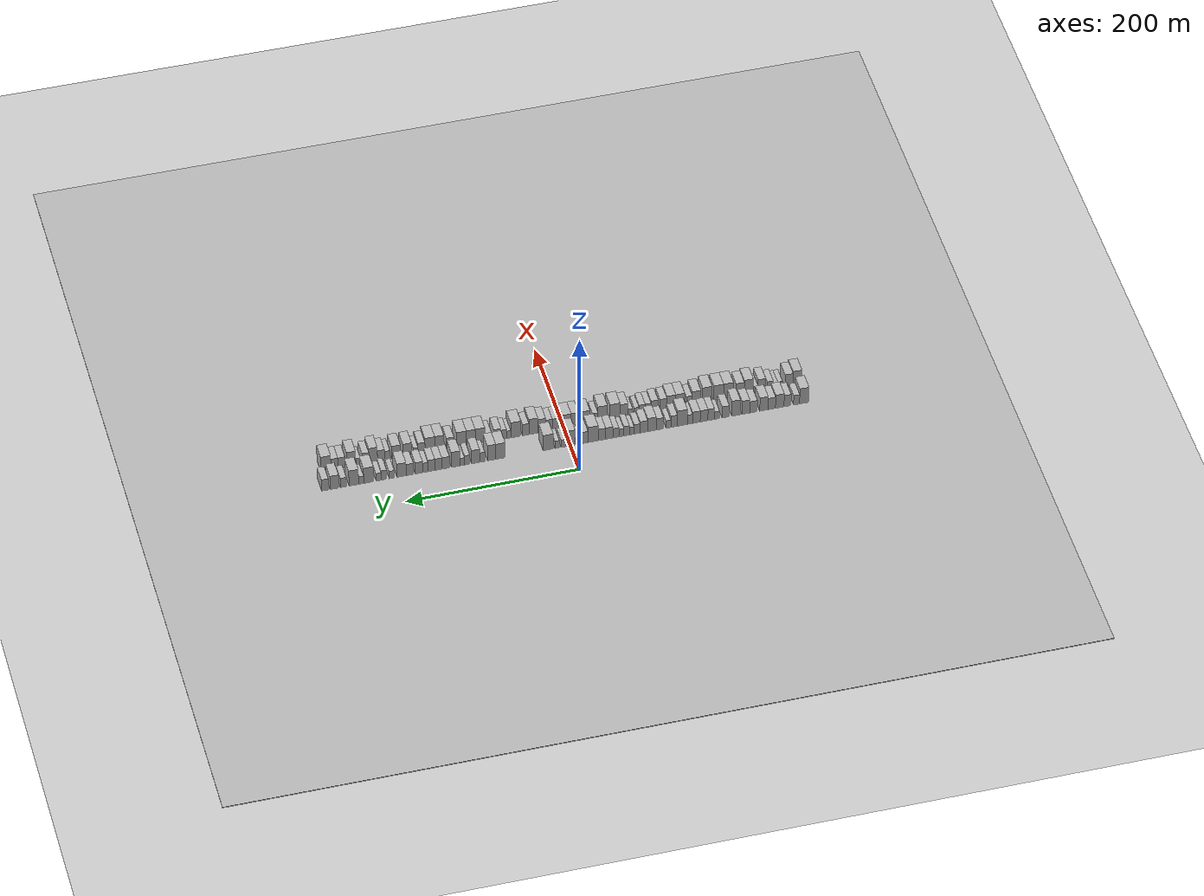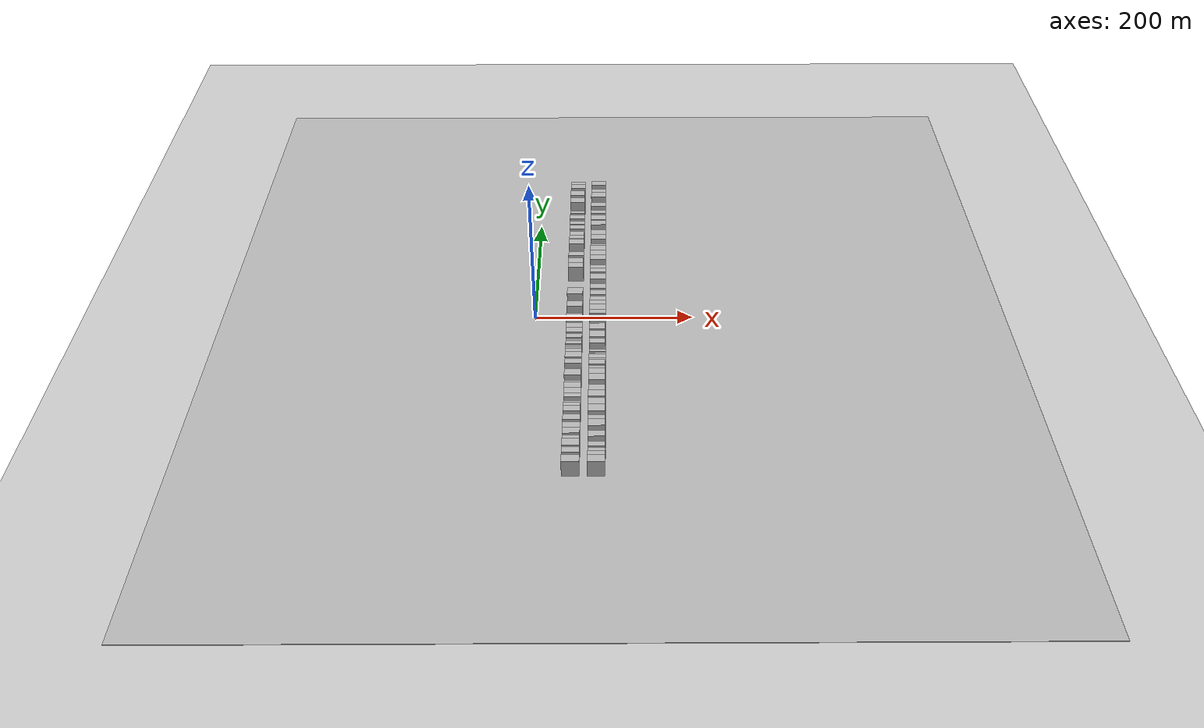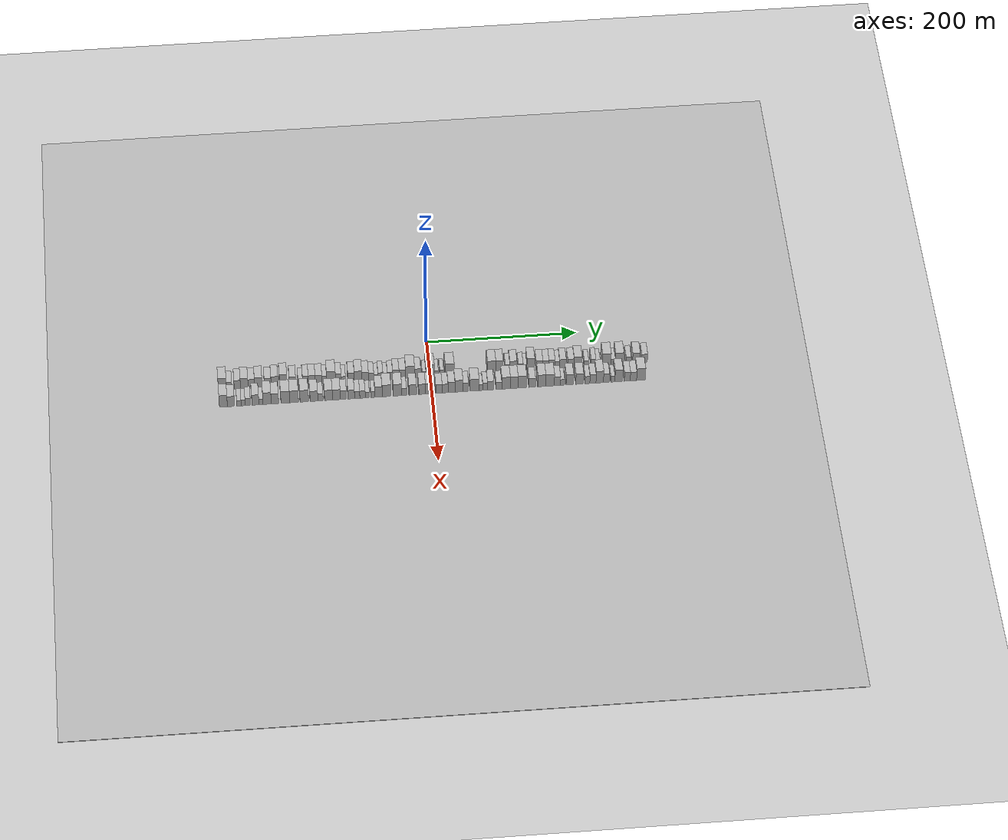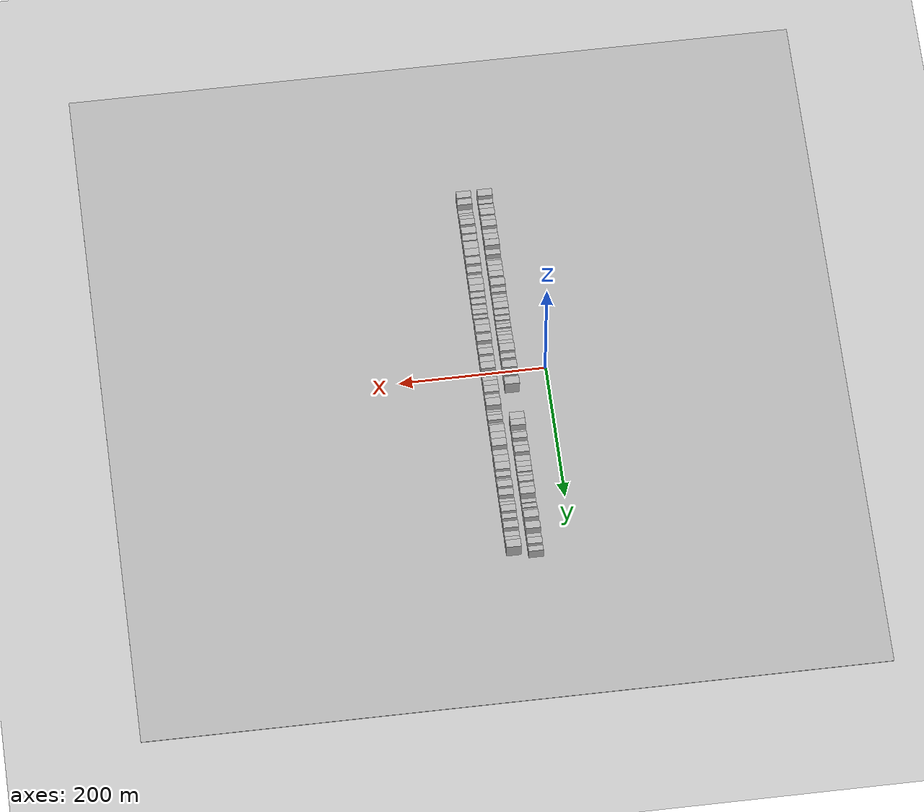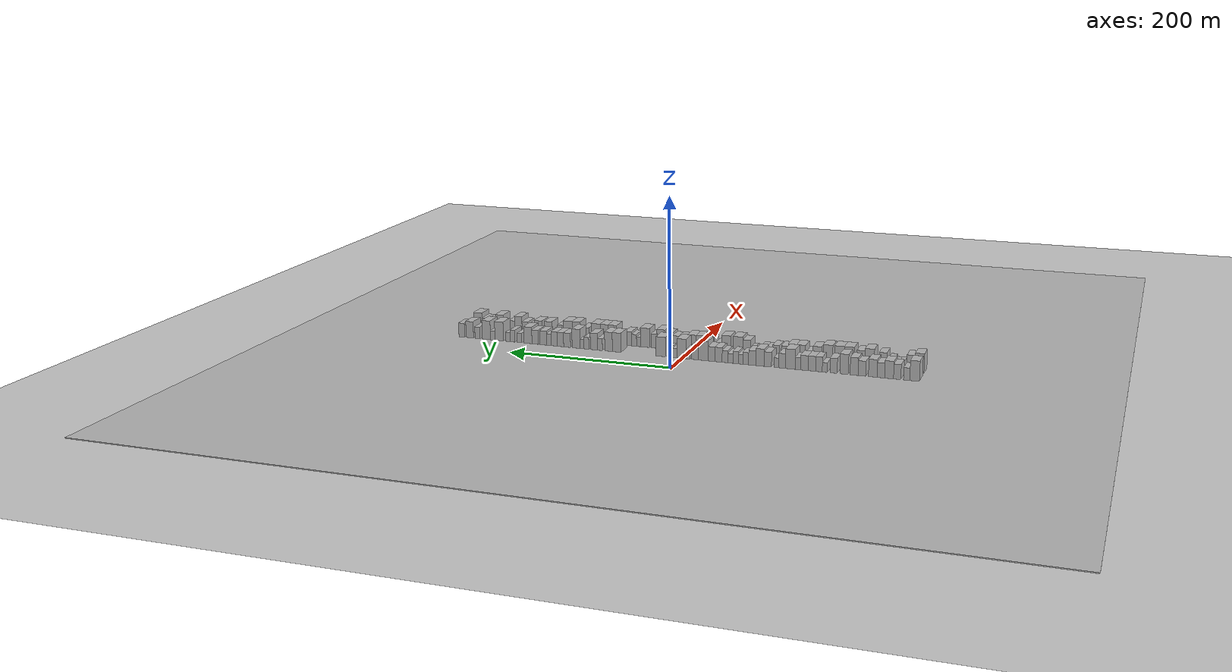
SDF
<?xml version="1.0" encoding="utf-8"?>

<sdf version="1.6">

   <world name="default">

      <gui fullscreen="0">

         <camera name="user_camera">

            <pose>-15 0 4.57585 0 0 0</pose>

            <view_controller>orbit</view_controller>

         </camera>

      </gui>

      <scene>

         <sky>

           <clouds>

             <speed>12</speed>

           </clouds>

         </sky>

         <ambient>0.4 0.4 0.4 1</ambient>

         <background>0.7 0.7 0.7 1</background>

         <shadows>1</shadows>

      </scene>

      <gravity>0 0 -9.8066</gravity>

      <magnetic_field>6e-06 2.3e-05 -4.2e-05</magnetic_field>

      <physics default="0" name="default_physics" type="ode">

         <ode>

            <solver>

               <type>quick</type>

               <iters>10</iters>

               <sor>1.0</sor>

               <use_dynamic_moi_rescaling>0</use_dynamic_moi_rescaling>

            </solver>

            <constraints>

               <cfm>0</cfm>

               <erp>0.2</erp>

               <contact_max_correcting_vel>100</contact_max_correcting_vel>

               <contact_surface_layer>0.001</contact_surface_layer>

            </constraints>

         </ode>

         <max_step_size>0.004</max_step_size>

         <real_time_factor>1</real_time_factor>

         <real_time_update_rate>250</real_time_update_rate>

      </physics>

      <light name="sun" type="directional">

         <cast_shadows>1</cast_shadows>

         <pose>0 0 10 0 0 0</pose>

         <diffuse>0.8 0.8 0.8 1</diffuse>

         <specular>0.2 0.2 0.2 1</specular>

         <attenuation>

            <range>1000</range>

            <constant>0.9</constant>

            <linear>0.01</linear>

            <quadratic>0.001</quadratic>

         </attenuation>

         <direction>-0.5 0.1 -0.9</direction>

      </light>

      <include>

         <name>ground_plane_1</name>

         <uri>model://HANNAS_ground_plane</uri>

         <pose>0 0 0  0 0 0</pose>

      </include>

      <include>

         <name>ground_plane_2</name>

         <uri>model://HANNAS_ground_plane</uri>

         <pose>100 0 0  0 0 0</pose>

      </include>

      <model name="building_1">

         <static>1</static>

         <pose frame="">50.0000 -272.6095 0 0.000000 0.000000 0.000000</pose>

         <link name="link">

            <pose frame="">0 0 12.00 0 0 0</pose>

            <collision name="collision">

               <geometry>

                  <box>

                     <size>20.0000 10.7811 24.0000</size>

                  </box>

               </geometry>

               <max_contacts>10</max_contacts>

               <surface>

                  <contact>

                     <ode/>

                  </contact>

                  <bounce/>

                  <friction>

                     <torsional>

                        <ode/>

                     </torsional>

                     <ode/>

                  </friction>

               </surface>

            </collision>

            <visual name="visual">

               <cast_shadows>0</cast_shadows>

               <geometry>

                  <box>

                     <size>20.0000 10.7811 24.0000</size>

                  </box>

               </geometry>

               <material>

                  <script>

                     <uri>model://HANNAS_wall/materials/scripts</uri>

                     <uri>model://HANNAS_wall/materials/textures</uri>

                     <name>vrc/HANNAS_wall</name>

                  </script>

               </material>

            </visual>

            <self_collide>0</self_collide>

            <enable_wind>0</enable_wind>

            <kinematic>0</kinematic>

         </link>

      </model>

      <model name="building_2">

         <static>1</static>

         <pose frame="">50.0000 -263.6989 0 0.000000 0.000000 0.000000</pose>

         <link name="link">

            <pose frame="">0 0 7.50 0 0 0</pose>

            <collision name="collision">

               <geometry>

                  <box>

                     <size>20.0000 7.0400 15.0000</size>

                  </box>

               </geometry>

               <max_contacts>10</max_contacts>

               <surface>

                  <contact>

                     <ode/>

                  </contact>

                  <bounce/>

                  <friction>

                     <torsional>

                        <ode/>

                     </torsional>

                     <ode/>

                  </friction>

               </surface>

            </collision>

            <visual name="visual">

               <cast_shadows>0</cast_shadows>

               <geometry>

                  <box>

                     <size>20.0000 7.0400 15.0000</size>

                  </box>

               </geometry>

               <material>

                  <script>

                     <uri>model://HANNAS_wall/materials/scripts</uri>

                     <uri>model://HANNAS_wall/materials/textures</uri>

                     <name>vrc/HANNAS_wall</name>

                  </script>

               </material>

            </visual>

            <self_collide>0</self_collide>

            <enable_wind>0</enable_wind>

            <kinematic>0</kinematic>

         </link>

      </model>

      <model name="building_3">

         <static>1</static>

         <pose frame="">50.0000 -253.0699 0 0.000000 0.000000 0.000000</pose>

         <link name="link">

            <pose frame="">0 0 9.00 0 0 0</pose>

            <collision name="collision">

               <geometry>

                  <box>

                     <size>20.0000 8.2181 18.0000</size>

                  </box>

               </geometry>

               <max_contacts>10</max_contacts>

               <surface>

                  <contact>

                     <ode/>

                  </contact>

                  <bounce/>

                  <friction>

                     <torsional>

                        <ode/>

                     </torsional>

                     <ode/>

                  </friction>

               </surface>

            </collision>

            <visual name="visual">

               <cast_shadows>0</cast_shadows>

               <geometry>

                  <box>

                     <size>20.0000 8.2181 18.0000</size>

                  </box>

               </geometry>

               <material>

                  <script>

                     <uri>model://HANNAS_wall/materials/scripts</uri>

                     <uri>model://HANNAS_wall/materials/textures</uri>

                     <name>vrc/HANNAS_wall</name>

                  </script>

               </material>

            </visual>

            <self_collide>0</self_collide>

            <enable_wind>0</enable_wind>

            <kinematic>0</kinematic>

         </link>

      </model>

      <model name="building_4">

         <static>1</static>

         <pose frame="">50.0000 -243.9424 0 0.000000 0.000000 0.000000</pose>

         <link name="link">

            <pose frame="">0 0 10.50 0 0 0</pose>

            <collision name="collision">

               <geometry>

                  <box>

                     <size>20.0000 10.0370 21.0000</size>

                  </box>

               </geometry>

               <max_contacts>10</max_contacts>

               <surface>

                  <contact>

                     <ode/>

                  </contact>

                  <bounce/>

                  <friction>

                     <torsional>

                        <ode/>

                     </torsional>

                     <ode/>

                  </friction>

               </surface>

            </collision>

            <visual name="visual">

               <cast_shadows>0</cast_shadows>

               <geometry>

                  <box>

                     <size>20.0000 10.0370 21.0000</size>

                  </box>

               </geometry>

               <material>

                  <script>

                     <uri>model://HANNAS_wall/materials/scripts</uri>

                     <uri>model://HANNAS_wall/materials/textures</uri>

                     <name>vrc/HANNAS_wall</name>

                  </script>

               </material>

            </visual>

            <self_collide>0</self_collide>

            <enable_wind>0</enable_wind>

            <kinematic>0</kinematic>

         </link>

      </model>

      <model name="building_5">

         <static>1</static>

         <pose frame="">50.0000 -234.6155 0 0.000000 0.000000 0.000000</pose>

         <link name="link">

            <pose frame="">0 0 9.00 0 0 0</pose>

            <collision name="collision">

               <geometry>

                  <box>

                     <size>20.0000 8.6167 18.0000</size>

                  </box>

               </geometry>

               <max_contacts>10</max_contacts>

               <surface>

                  <contact>

                     <ode/>

                  </contact>

                  <bounce/>

                  <friction>

                     <torsional>

                        <ode/>

                     </torsional>

                     <ode/>

                  </friction>

               </surface>

            </collision>

            <visual name="visual">

               <cast_shadows>0</cast_shadows>

               <geometry>

                  <box>

                     <size>20.0000 8.6167 18.0000</size>

                  </box>

               </geometry>

               <material>

                  <script>

                     <uri>model://HANNAS_wall/materials/scripts</uri>

                     <uri>model://HANNAS_wall/materials/textures</uri>

                     <name>vrc/HANNAS_wall</name>

                  </script>

               </material>

            </visual>

            <self_collide>0</self_collide>

            <enable_wind>0</enable_wind>

            <kinematic>0</kinematic>

         </link>

      </model>

      <model name="building_6">

         <static>1</static>

         <pose frame="">50.0000 -225.4179 0 0.000000 0.000000 0.000000</pose>

         <link name="link">

            <pose frame="">0 0 10.50 0 0 0</pose>

            <collision name="collision">

               <geometry>

                  <box>

                     <size>20.0000 9.7786 21.0000</size>

                  </box>

               </geometry>

               <max_contacts>10</max_contacts>

               <surface>

                  <contact>

                     <ode/>

                  </contact>

                  <bounce/>

                  <friction>

                     <torsional>

                        <ode/>

                     </torsional>

                     <ode/>

                  </friction>

               </surface>

            </collision>

            <visual name="visual">

               <cast_shadows>0</cast_shadows>

               <geometry>

                  <box>

                     <size>20.0000 9.7786 21.0000</size>

                  </box>

               </geometry>

               <material>

                  <script>

                     <uri>model://HANNAS_wall/materials/scripts</uri>

                     <uri>model://HANNAS_wall/materials/textures</uri>

                     <name>vrc/HANNAS_wall</name>

                  </script>

               </material>

            </visual>

            <self_collide>0</self_collide>

            <enable_wind>0</enable_wind>

            <kinematic>0</kinematic>

         </link>

      </model>

      <model name="building_7">

         <static>1</static>

         <pose frame="">50.0000 -213.1358 0 0.000000 0.000000 0.000000</pose>

         <link name="link">

            <pose frame="">0 0 9.00 0 0 0</pose>

            <collision name="collision">

               <geometry>

                  <box>

                     <size>20.0000 8.7856 18.0000</size>

                  </box>

               </geometry>

               <max_contacts>10</max_contacts>

               <surface>

                  <contact>

                     <ode/>

                  </contact>

                  <bounce/>

                  <friction>

                     <torsional>

                        <ode/>

                     </torsional>

                     <ode/>

                  </friction>

               </surface>

            </collision>

            <visual name="visual">

               <cast_shadows>0</cast_shadows>

               <geometry>

                  <box>

                     <size>20.0000 8.7856 18.0000</size>

                  </box>

               </geometry>

               <material>

                  <script>

                     <uri>model://HANNAS_wall/materials/scripts</uri>

                     <uri>model://HANNAS_wall/materials/textures</uri>

                     <name>vrc/HANNAS_wall</name>

                  </script>

               </material>

            </visual>

            <self_collide>0</self_collide>

            <enable_wind>0</enable_wind>

            <kinematic>0</kinematic>

         </link>

      </model>

      <model name="building_8">

         <static>1</static>

         <pose frame="">50.0000 -204.1743 0 0.000000 0.000000 0.000000</pose>

         <link name="link">

            <pose frame="">0 0 10.50 0 0 0</pose>

            <collision name="collision">

               <geometry>

                  <box>

                     <size>20.0000 9.1375 21.0000</size>

                  </box>

               </geometry>

               <max_contacts>10</max_contacts>

               <surface>

                  <contact>

                     <ode/>

                  </contact>

                  <bounce/>

                  <friction>

                     <torsional>

                        <ode/>

                     </torsional>

                     <ode/>

                  </friction>

               </surface>

            </collision>

            <visual name="visual">

               <cast_shadows>0</cast_shadows>

               <geometry>

                  <box>

                     <size>20.0000 9.1375 21.0000</size>

                  </box>

               </geometry>

               <material>

                  <script>

                     <uri>model://HANNAS_wall/materials/scripts</uri>

                     <uri>model://HANNAS_wall/materials/textures</uri>

                     <name>vrc/HANNAS_wall</name>

                  </script>

               </material>

            </visual>

            <self_collide>0</self_collide>

            <enable_wind>0</enable_wind>

            <kinematic>0</kinematic>

         </link>

      </model>

      <model name="building_9">

         <static>1</static>

         <pose frame="">50.0000 -192.6847 0 0.000000 0.000000 0.000000</pose>

         <link name="link">

            <pose frame="">0 0 12.00 0 0 0</pose>

            <collision name="collision">

               <geometry>

                  <box>

                     <size>20.0000 9.8418 24.0000</size>

                  </box>

               </geometry>

               <max_contacts>10</max_contacts>

               <surface>

                  <contact>

                     <ode/>

                  </contact>

                  <bounce/>

                  <friction>

                     <torsional>

                        <ode/>

                     </torsional>

                     <ode/>

                  </friction>

               </surface>

            </collision>

            <visual name="visual">

               <cast_shadows>0</cast_shadows>

               <geometry>

                  <box>

                     <size>20.0000 9.8418 24.0000</size>

                  </box>

               </geometry>

               <material>

                  <script>

                     <uri>model://HANNAS_wall/materials/scripts</uri>

                     <uri>model://HANNAS_wall/materials/textures</uri>

                     <name>vrc/HANNAS_wall</name>

                  </script>

               </material>

            </visual>

            <self_collide>0</self_collide>

            <enable_wind>0</enable_wind>

            <kinematic>0</kinematic>

         </link>

      </model>

      <model name="building_10">

         <static>1</static>

         <pose frame="">50.0000 -180.5605 0 0.000000 0.000000 0.000000</pose>

         <link name="link">

            <pose frame="">0 0 9.00 0 0 0</pose>

            <collision name="collision">

               <geometry>

                  <box>

                     <size>20.0000 8.4065 18.0000</size>

                  </box>

               </geometry>

               <max_contacts>10</max_contacts>

               <surface>

                  <contact>

                     <ode/>

                  </contact>

                  <bounce/>

                  <friction>

                     <torsional>

                        <ode/>

                     </torsional>

                     <ode/>

                  </friction>

               </surface>

            </collision>

            <visual name="visual">

               <cast_shadows>0</cast_shadows>

               <geometry>

                  <box>

                     <size>20.0000 8.4065 18.0000</size>

                  </box>

               </geometry>

               <material>

                  <script>

                     <uri>model://HANNAS_wall/materials/scripts</uri>

                     <uri>model://HANNAS_wall/materials/textures</uri>

                     <name>vrc/HANNAS_wall</name>

                  </script>

               </material>

            </visual>

            <self_collide>0</self_collide>

            <enable_wind>0</enable_wind>

            <kinematic>0</kinematic>

         </link>

      </model>

      <model name="building_11">

         <static>1</static>

         <pose frame="">50.0000 -170.3896 0 0.000000 0.000000 0.000000</pose>

         <link name="link">

            <pose frame="">0 0 6.00 0 0 0</pose>

            <collision name="collision">

               <geometry>

                  <box>

                     <size>20.0000 5.9353 12.0000</size>

                  </box>

               </geometry>

               <max_contacts>10</max_contacts>

               <surface>

                  <contact>

                     <ode/>

                  </contact>

                  <bounce/>

                  <friction>

                     <torsional>

                        <ode/>

                     </torsional>

                     <ode/>

                  </friction>

               </surface>

            </collision>

            <visual name="visual">

               <cast_shadows>0</cast_shadows>

               <geometry>

                  <box>

                     <size>20.0000 5.9353 12.0000</size>

                  </box>

               </geometry>

               <material>

                  <script>

                     <uri>model://HANNAS_wall/materials/scripts</uri>

                     <uri>model://HANNAS_wall/materials/textures</uri>

                     <name>vrc/HANNAS_wall</name>

                  </script>

               </material>

            </visual>

            <self_collide>0</self_collide>

            <enable_wind>0</enable_wind>

            <kinematic>0</kinematic>

         </link>

      </model>

      <model name="building_12">

         <static>1</static>

         <pose frame="">50.0000 -163.6053 0 0.000000 0.000000 0.000000</pose>

         <link name="link">

            <pose frame="">0 0 9.00 0 0 0</pose>

            <collision name="collision">

               <geometry>

                  <box>

                     <size>20.0000 7.6333 18.0000</size>

                  </box>

               </geometry>

               <max_contacts>10</max_contacts>

               <surface>

                  <contact>

                     <ode/>

                  </contact>

                  <bounce/>

                  <friction>

                     <torsional>

                        <ode/>

                     </torsional>

                     <ode/>

                  </friction>

               </surface>

            </collision>

            <visual name="visual">

               <cast_shadows>0</cast_shadows>

               <geometry>

                  <box>

                     <size>20.0000 7.6333 18.0000</size>

                  </box>

               </geometry>

               <material>

                  <script>

                     <uri>model://HANNAS_wall/materials/scripts</uri>

                     <uri>model://HANNAS_wall/materials/textures</uri>

                     <name>vrc/HANNAS_wall</name>

                  </script>

               </material>

            </visual>

            <self_collide>0</self_collide>

            <enable_wind>0</enable_wind>

            <kinematic>0</kinematic>

         </link>

      </model>

      <model name="building_13">

         <static>1</static>

         <pose frame="">50.0000 -155.2934 0 0.000000 0.000000 0.000000</pose>

         <link name="link">

            <pose frame="">0 0 9.00 0 0 0</pose>

            <collision name="collision">

               <geometry>

                  <box>

                     <size>20.0000 8.9907 18.0000</size>

                  </box>

               </geometry>

               <max_contacts>10</max_contacts>

               <surface>

                  <contact>

                     <ode/>

                  </contact>

                  <bounce/>

                  <friction>

                     <torsional>

                        <ode/>

                     </torsional>

                     <ode/>

                  </friction>

               </surface>

            </collision>

            <visual name="visual">

               <cast_shadows>0</cast_shadows>

               <geometry>

                  <box>

                     <size>20.0000 8.9907 18.0000</size>

                  </box>

               </geometry>

               <material>

                  <script>

                     <uri>model://HANNAS_wall/materials/scripts</uri>

                     <uri>model://HANNAS_wall/materials/textures</uri>

                     <name>vrc/HANNAS_wall</name>

                  </script>

               </material>

            </visual>

            <self_collide>0</self_collide>

            <enable_wind>0</enable_wind>

            <kinematic>0</kinematic>

         </link>

      </model>

      <model name="building_14">

         <static>1</static>

         <pose frame="">50.0000 -146.3652 0 0.000000 0.000000 0.000000</pose>

         <link name="link">

            <pose frame="">0 0 9.00 0 0 0</pose>

            <collision name="collision">

               <geometry>

                  <box>

                     <size>20.0000 8.8655 18.0000</size>

                  </box>

               </geometry>

               <max_contacts>10</max_contacts>

               <surface>

                  <contact>

                     <ode/>

                  </contact>

                  <bounce/>

                  <friction>

                     <torsional>

                        <ode/>

                     </torsional>

                     <ode/>

                  </friction>

               </surface>

            </collision>

            <visual name="visual">

               <cast_shadows>0</cast_shadows>

               <geometry>

                  <box>

                     <size>20.0000 8.8655 18.0000</size>

                  </box>

               </geometry>

               <material>

                  <script>

                     <uri>model://HANNAS_wall/materials/scripts</uri>

                     <uri>model://HANNAS_wall/materials/textures</uri>

                     <name>vrc/HANNAS_wall</name>

                  </script>

               </material>

            </visual>

            <self_collide>0</self_collide>

            <enable_wind>0</enable_wind>

            <kinematic>0</kinematic>

         </link>

      </model>

      <model name="building_15">

         <static>1</static>

         <pose frame="">50.0000 -138.8571 0 0.000000 0.000000 0.000000</pose>

         <link name="link">

            <pose frame="">0 0 7.50 0 0 0</pose>

            <collision name="collision">

               <geometry>

                  <box>

                     <size>20.0000 6.1508 15.0000</size>

                  </box>

               </geometry>

               <max_contacts>10</max_contacts>

               <surface>

                  <contact>

                     <ode/>

                  </contact>

                  <bounce/>

                  <friction>

                     <torsional>

                        <ode/>

                     </torsional>

                     <ode/>

                  </friction>

               </surface>

            </collision>

            <visual name="visual">

               <cast_shadows>0</cast_shadows>

               <geometry>

                  <box>

                     <size>20.0000 6.1508 15.0000</size>

                  </box>

               </geometry>

               <material>

                  <script>

                     <uri>model://HANNAS_wall/materials/scripts</uri>

                     <uri>model://HANNAS_wall/materials/textures</uri>

                     <name>vrc/HANNAS_wall</name>

                  </script>

               </material>

            </visual>

            <self_collide>0</self_collide>

            <enable_wind>0</enable_wind>

            <kinematic>0</kinematic>

         </link>

      </model>

      <model name="building_16">

         <static>1</static>

         <pose frame="">50.0000 -130.0185 0 0.000000 0.000000 0.000000</pose>

         <link name="link">

            <pose frame="">0 0 12.00 0 0 0</pose>

            <collision name="collision">

               <geometry>

                  <box>

                     <size>20.0000 11.5264 24.0000</size>

                  </box>

               </geometry>

               <max_contacts>10</max_contacts>

               <surface>

                  <contact>

                     <ode/>

                  </contact>

                  <bounce/>

                  <friction>

                     <torsional>

                        <ode/>

                     </torsional>

                     <ode/>

                  </friction>

               </surface>

            </collision>

            <visual name="visual">

               <cast_shadows>0</cast_shadows>

               <geometry>

                  <box>

                     <size>20.0000 11.5264 24.0000</size>

                  </box>

               </geometry>

               <material>

                  <script>

                     <uri>model://HANNAS_wall/materials/scripts</uri>

                     <uri>model://HANNAS_wall/materials/textures</uri>

                     <name>vrc/HANNAS_wall</name>

                  </script>

               </material>

            </visual>

            <self_collide>0</self_collide>

            <enable_wind>0</enable_wind>

            <kinematic>0</kinematic>

         </link>

      </model>

      <model name="building_17">

         <static>1</static>

         <pose frame="">50.0000 -120.4466 0 0.000000 0.000000 0.000000</pose>

         <link name="link">

            <pose frame="">0 0 9.00 0 0 0</pose>

            <collision name="collision">

               <geometry>

                  <box>

                     <size>20.0000 7.6174 18.0000</size>

                  </box>

               </geometry>

               <max_contacts>10</max_contacts>

               <surface>

                  <contact>

                     <ode/>

                  </contact>

                  <bounce/>

                  <friction>

                     <torsional>

                        <ode/>

                     </torsional>

                     <ode/>

                  </friction>

               </surface>

            </collision>

            <visual name="visual">

               <cast_shadows>0</cast_shadows>

               <geometry>

                  <box>

                     <size>20.0000 7.6174 18.0000</size>

                  </box>

               </geometry>

               <material>

                  <script>

                     <uri>model://HANNAS_wall/materials/scripts</uri>

                     <uri>model://HANNAS_wall/materials/textures</uri>

                     <name>vrc/HANNAS_wall</name>

                  </script>

               </material>

            </visual>

            <self_collide>0</self_collide>

            <enable_wind>0</enable_wind>

            <kinematic>0</kinematic>

         </link>

      </model>

      <model name="building_18">

         <static>1</static>

         <pose frame="">50.0000 -113.7780 0 0.000000 0.000000 0.000000</pose>

         <link name="link">

            <pose frame="">0 0 6.00 0 0 0</pose>

            <collision name="collision">

               <geometry>

                  <box>

                     <size>20.0000 5.7198 12.0000</size>

                  </box>

               </geometry>

               <max_contacts>10</max_contacts>

               <surface>

                  <contact>

                     <ode/>

                  </contact>

                  <bounce/>

                  <friction>

                     <torsional>

                        <ode/>

                     </torsional>

                     <ode/>

                  </friction>

               </surface>

            </collision>

            <visual name="visual">

               <cast_shadows>0</cast_shadows>

               <geometry>

                  <box>

                     <size>20.0000 5.7198 12.0000</size>

                  </box>

               </geometry>

               <material>

                  <script>

                     <uri>model://HANNAS_wall/materials/scripts</uri>

                     <uri>model://HANNAS_wall/materials/textures</uri>

                     <name>vrc/HANNAS_wall</name>

                  </script>

               </material>

            </visual>

            <self_collide>0</self_collide>

            <enable_wind>0</enable_wind>

            <kinematic>0</kinematic>

         </link>

      </model>

      <model name="building_19">

         <static>1</static>

         <pose frame="">50.0000 -103.6759 0 0.000000 0.000000 0.000000</pose>

         <link name="link">

            <pose frame="">0 0 9.00 0 0 0</pose>

            <collision name="collision">

               <geometry>

                  <box>

                     <size>20.0000 8.4845 18.0000</size>

                  </box>

               </geometry>

               <max_contacts>10</max_contacts>

               <surface>

                  <contact>

                     <ode/>

                  </contact>

                  <bounce/>

                  <friction>

                     <torsional>

                        <ode/>

                     </torsional>

                     <ode/>

                  </friction>

               </surface>

            </collision>

            <visual name="visual">

               <cast_shadows>0</cast_shadows>

               <geometry>

                  <box>

                     <size>20.0000 8.4845 18.0000</size>

                  </box>

               </geometry>

               <material>

                  <script>

                     <uri>model://HANNAS_wall/materials/scripts</uri>

                     <uri>model://HANNAS_wall/materials/textures</uri>

                     <name>vrc/HANNAS_wall</name>

                  </script>

               </material>

            </visual>

            <self_collide>0</self_collide>

            <enable_wind>0</enable_wind>

            <kinematic>0</kinematic>

         </link>

      </model>

      <model name="building_20">

         <static>1</static>

         <pose frame="">50.0000 -94.4692 0 0.000000 0.000000 0.000000</pose>

         <link name="link">

            <pose frame="">0 0 10.50 0 0 0</pose>

            <collision name="collision">

               <geometry>

                  <box>

                     <size>20.0000 9.9289 21.0000</size>

                  </box>

               </geometry>

               <max_contacts>10</max_contacts>

               <surface>

                  <contact>

                     <ode/>

                  </contact>

                  <bounce/>

                  <friction>

                     <torsional>

                        <ode/>

                     </torsional>

                     <ode/>

                  </friction>

               </surface>

            </collision>

            <visual name="visual">

               <cast_shadows>0</cast_shadows>

               <geometry>

                  <box>

                     <size>20.0000 9.9289 21.0000</size>

                  </box>

               </geometry>

               <material>

                  <script>

                     <uri>model://HANNAS_wall/materials/scripts</uri>

                     <uri>model://HANNAS_wall/materials/textures</uri>

                     <name>vrc/HANNAS_wall</name>

                  </script>

               </material>

            </visual>

            <self_collide>0</self_collide>

            <enable_wind>0</enable_wind>

            <kinematic>0</kinematic>

         </link>

      </model>

      <model name="building_21">

         <static>1</static>

         <pose frame="">50.0000 -85.1361 0 0.000000 0.000000 0.000000</pose>

         <link name="link">

            <pose frame="">0 0 9.00 0 0 0</pose>

            <collision name="collision">

               <geometry>

                  <box>

                     <size>20.0000 8.7373 18.0000</size>

                  </box>

               </geometry>

               <max_contacts>10</max_contacts>

               <surface>

                  <contact>

                     <ode/>

                  </contact>

                  <bounce/>

                  <friction>

                     <torsional>

                        <ode/>

                     </torsional>

                     <ode/>

                  </friction>

               </surface>

            </collision>

            <visual name="visual">

               <cast_shadows>0</cast_shadows>

               <geometry>

                  <box>

                     <size>20.0000 8.7373 18.0000</size>

                  </box>

               </geometry>

               <material>

                  <script>

                     <uri>model://HANNAS_wall/materials/scripts</uri>

                     <uri>model://HANNAS_wall/materials/textures</uri>

                     <name>vrc/HANNAS_wall</name>

                  </script>

               </material>

            </visual>

            <self_collide>0</self_collide>

            <enable_wind>0</enable_wind>

            <kinematic>0</kinematic>

         </link>

      </model>

      <model name="building_22">

         <static>1</static>

         <pose frame="">50.0000 -77.2666 0 0.000000 0.000000 0.000000</pose>

         <link name="link">

            <pose frame="">0 0 7.50 0 0 0</pose>

            <collision name="collision">

               <geometry>

                  <box>

                     <size>20.0000 7.0017 15.0000</size>

                  </box>

               </geometry>

               <max_contacts>10</max_contacts>

               <surface>

                  <contact>

                     <ode/>

                  </contact>

                  <bounce/>

                  <friction>

                     <torsional>

                        <ode/>

                     </torsional>

                     <ode/>

                  </friction>

               </surface>

            </collision>

            <visual name="visual">

               <cast_shadows>0</cast_shadows>

               <geometry>

                  <box>

                     <size>20.0000 7.0017 15.0000</size>

                  </box>

               </geometry>

               <material>

                  <script>

                     <uri>model://HANNAS_wall/materials/scripts</uri>

                     <uri>model://HANNAS_wall/materials/textures</uri>

                     <name>vrc/HANNAS_wall</name>

                  </script>

               </material>

            </visual>

            <self_collide>0</self_collide>

            <enable_wind>0</enable_wind>

            <kinematic>0</kinematic>

         </link>

      </model>

      <model name="building_23">

         <static>1</static>

         <pose frame="">50.0000 -71.0025 0 0.000000 0.000000 0.000000</pose>

         <link name="link">

            <pose frame="">0 0 6.00 0 0 0</pose>

            <collision name="collision">

               <geometry>

                  <box>

                     <size>20.0000 5.5265 12.0000</size>

                  </box>

               </geometry>

               <max_contacts>10</max_contacts>

               <surface>

                  <contact>

                     <ode/>

                  </contact>

                  <bounce/>

                  <friction>

                     <torsional>

                        <ode/>

                     </torsional>

                     <ode/>

                  </friction>

               </surface>

            </collision>

            <visual name="visual">

               <cast_shadows>0</cast_shadows>

               <geometry>

                  <box>

                     <size>20.0000 5.5265 12.0000</size>

                  </box>

               </geometry>

               <material>

                  <script>

                     <uri>model://HANNAS_wall/materials/scripts</uri>

                     <uri>model://HANNAS_wall/materials/textures</uri>

                     <name>vrc/HANNAS_wall</name>

                  </script>

               </material>

            </visual>

            <self_collide>0</self_collide>

            <enable_wind>0</enable_wind>

            <kinematic>0</kinematic>

         </link>

      </model>

      <model name="building_24">

         <static>1</static>

         <pose frame="">50.0000 -65.0267 0 0.000000 0.000000 0.000000</pose>

         <link name="link">

            <pose frame="">0 0 7.50 0 0 0</pose>

            <collision name="collision">

               <geometry>

                  <box>

                     <size>20.0000 6.4250 15.0000</size>

                  </box>

               </geometry>

               <max_contacts>10</max_contacts>

               <surface>

                  <contact>

                     <ode/>

                  </contact>

                  <bounce/>

                  <friction>

                     <torsional>

                        <ode/>

                     </torsional>

                     <ode/>

                  </friction>

               </surface>

            </collision>

            <visual name="visual">

               <cast_shadows>0</cast_shadows>

               <geometry>

                  <box>

                     <size>20.0000 6.4250 15.0000</size>

                  </box>

               </geometry>

               <material>

                  <script>

                     <uri>model://HANNAS_wall/materials/scripts</uri>

                     <uri>model://HANNAS_wall/materials/textures</uri>

                     <name>vrc/HANNAS_wall</name>

                  </script>

               </material>

            </visual>

            <self_collide>0</self_collide>

            <enable_wind>0</enable_wind>

            <kinematic>0</kinematic>

         </link>

      </model>

      <model name="building_25">

         <static>1</static>

         <pose frame="">50.0000 -58.8759 0 0.000000 0.000000 0.000000</pose>

         <link name="link">

            <pose frame="">0 0 6.00 0 0 0</pose>

            <collision name="collision">

               <geometry>

                  <box>

                     <size>20.0000 5.8766 12.0000</size>

                  </box>

               </geometry>

               <max_contacts>10</max_contacts>

               <surface>

                  <contact>

                     <ode/>

                  </contact>

                  <bounce/>

                  <friction>

                     <torsional>

                        <ode/>

                     </torsional>

                     <ode/>

                  </friction>

               </surface>

            </collision>

            <visual name="visual">

               <cast_shadows>0</cast_shadows>

               <geometry>

                  <box>

                     <size>20.0000 5.8766 12.0000</size>

                  </box>

               </geometry>

               <material>

                  <script>

                     <uri>model://HANNAS_wall/materials/scripts</uri>

                     <uri>model://HANNAS_wall/materials/textures</uri>

                     <name>vrc/HANNAS_wall</name>

                  </script>

               </material>

            </visual>

            <self_collide>0</self_collide>

            <enable_wind>0</enable_wind>

            <kinematic>0</kinematic>

         </link>

      </model>

      <model name="building_26">

         <static>1</static>

         <pose frame="">50.0000 -52.4413 0 0.000000 0.000000 0.000000</pose>

         <link name="link">

            <pose frame="">0 0 7.50 0 0 0</pose>

            <collision name="collision">

               <geometry>

                  <box>

                     <size>20.0000 6.9926 15.0000</size>

                  </box>

               </geometry>

               <max_contacts>10</max_contacts>

               <surface>

                  <contact>

                     <ode/>

                  </contact>

                  <bounce/>

                  <friction>

                     <torsional>

                        <ode/>

                     </torsional>

                     <ode/>

                  </friction>

               </surface>

            </collision>

            <visual name="visual">

               <cast_shadows>0</cast_shadows>

               <geometry>

                  <box>

                     <size>20.0000 6.9926 15.0000</size>

                  </box>

               </geometry>

               <material>

                  <script>

                     <uri>model://HANNAS_wall/materials/scripts</uri>

                     <uri>model://HANNAS_wall/materials/textures</uri>

                     <name>vrc/HANNAS_wall</name>

                  </script>

               </material>

            </visual>

            <self_collide>0</self_collide>

            <enable_wind>0</enable_wind>

            <kinematic>0</kinematic>

         </link>

      </model>

      <model name="building_27">

         <static>1</static>

         <pose frame="">50.0000 -44.7642 0 0.000000 0.000000 0.000000</pose>

         <link name="link">

            <pose frame="">0 0 9.00 0 0 0</pose>

            <collision name="collision">

               <geometry>

                  <box>

                     <size>20.0000 8.3615 18.0000</size>

                  </box>

               </geometry>

               <max_contacts>10</max_contacts>

               <surface>

                  <contact>

                     <ode/>

                  </contact>

                  <bounce/>

                  <friction>

                     <torsional>

                        <ode/>

                     </torsional>

                     <ode/>

                  </friction>

               </surface>

            </collision>

            <visual name="visual">

               <cast_shadows>0</cast_shadows>

               <geometry>

                  <box>

                     <size>20.0000 8.3615 18.0000</size>

                  </box>

               </geometry>

               <material>

                  <script>

                     <uri>model://HANNAS_wall/materials/scripts</uri>

                     <uri>model://HANNAS_wall/materials/textures</uri>

                     <name>vrc/HANNAS_wall</name>

                  </script>

               </material>

            </visual>

            <self_collide>0</self_collide>

            <enable_wind>0</enable_wind>

            <kinematic>0</kinematic>

         </link>

      </model>

      <model name="building_28">

         <static>1</static>

         <pose frame="">50.0000 -36.2077 0 0.000000 0.000000 0.000000</pose>

         <link name="link">

            <pose frame="">0 0 9.00 0 0 0</pose>

            <collision name="collision">

               <geometry>

                  <box>

                     <size>20.0000 8.7515 18.0000</size>

                  </box>

               </geometry>

               <max_contacts>10</max_contacts>

               <surface>

                  <contact>

                     <ode/>

                  </contact>

                  <bounce/>

                  <friction>

                     <torsional>

                        <ode/>

                     </torsional>

                     <ode/>

                  </friction>

               </surface>

            </collision>

            <visual name="visual">

               <cast_shadows>0</cast_shadows>

               <geometry>

                  <box>

                     <size>20.0000 8.7515 18.0000</size>

                  </box>

               </geometry>

               <material>

                  <script>

                     <uri>model://HANNAS_wall/materials/scripts</uri>

                     <uri>model://HANNAS_wall/materials/textures</uri>

                     <name>vrc/HANNAS_wall</name>

                  </script>

               </material>

            </visual>

            <self_collide>0</self_collide>

            <enable_wind>0</enable_wind>

            <kinematic>0</kinematic>

         </link>

      </model>

      <model name="building_29">

         <static>1</static>

         <pose frame="">50.0000 -25.9818 0 0.000000 0.000000 0.000000</pose>

         <link name="link">

            <pose frame="">0 0 12.00 0 0 0</pose>

            <collision name="collision">

               <geometry>

                  <box>

                     <size>20.0000 11.7005 24.0000</size>

                  </box>

               </geometry>

               <max_contacts>10</max_contacts>

               <surface>

                  <contact>

                     <ode/>

                  </contact>

                  <bounce/>

                  <friction>

                     <torsional>

                        <ode/>

                     </torsional>

                     <ode/>

                  </friction>

               </surface>

            </collision>

            <visual name="visual">

               <cast_shadows>0</cast_shadows>

               <geometry>

                  <box>

                     <size>20.0000 11.7005 24.0000</size>

                  </box>

               </geometry>

               <material>

                  <script>

                     <uri>model://HANNAS_wall/materials/scripts</uri>

                     <uri>model://HANNAS_wall/materials/textures</uri>

                     <name>vrc/HANNAS_wall</name>

                  </script>

               </material>

            </visual>

            <self_collide>0</self_collide>

            <enable_wind>0</enable_wind>

            <kinematic>0</kinematic>

         </link>

      </model>

      <model name="building_30">

         <static>1</static>

         <pose frame="">50.0000 -16.0936 0 0.000000 0.000000 0.000000</pose>

         <link name="link">

            <pose frame="">0 0 9.00 0 0 0</pose>

            <collision name="collision">

               <geometry>

                  <box>

                     <size>20.0000 8.0759 18.0000</size>

                  </box>

               </geometry>

               <max_contacts>10</max_contacts>

               <surface>

                  <contact>

                     <ode/>

                  </contact>

                  <bounce/>

                  <friction>

                     <torsional>

                        <ode/>

                     </torsional>

                     <ode/>

                  </friction>

               </surface>

            </collision>

            <visual name="visual">

               <cast_shadows>0</cast_shadows>

               <geometry>

                  <box>

                     <size>20.0000 8.0759 18.0000</size>

                  </box>

               </geometry>

               <material>

                  <script>

                     <uri>model://HANNAS_wall/materials/scripts</uri>

                     <uri>model://HANNAS_wall/materials/textures</uri>

                     <name>vrc/HANNAS_wall</name>

                  </script>

               </material>

            </visual>

            <self_collide>0</self_collide>

            <enable_wind>0</enable_wind>

            <kinematic>0</kinematic>

         </link>

      </model>

      <model name="building_31">

         <static>1</static>

         <pose frame="">50.0000 -7.6204 0 0.000000 0.000000 0.000000</pose>

         <link name="link">

            <pose frame="">0 0 6.00 0 0 0</pose>

            <collision name="collision">

               <geometry>

                  <box>

                     <size>20.0000 4.8705 12.0000</size>

                  </box>

               </geometry>

               <max_contacts>10</max_contacts>

               <surface>

                  <contact>

                     <ode/>

                  </contact>

                  <bounce/>

                  <friction>

                     <torsional>

                        <ode/>

                     </torsional>

                     <ode/>

                  </friction>

               </surface>

            </collision>

            <visual name="visual">

               <cast_shadows>0</cast_shadows>

               <geometry>

                  <box>

                     <size>20.0000 4.8705 12.0000</size>

                  </box>

               </geometry>

               <material>

                  <script>

                     <uri>model://HANNAS_wall/materials/scripts</uri>

                     <uri>model://HANNAS_wall/materials/textures</uri>

                     <name>vrc/HANNAS_wall</name>

                  </script>

               </material>

            </visual>

            <self_collide>0</self_collide>

            <enable_wind>0</enable_wind>

            <kinematic>0</kinematic>

         </link>

      </model>

      <model name="building_32">

         <static>1</static>

         <pose frame="">50.0000 0.3281 0 0.000000 0.000000 0.000000</pose>

         <link name="link">

            <pose frame="">0 0 12.00 0 0 0</pose>

            <collision name="collision">

               <geometry>

                  <box>

                     <size>20.0000 11.0267 24.0000</size>

                  </box>

               </geometry>

               <max_contacts>10</max_contacts>

               <surface>

                  <contact>

                     <ode/>

                  </contact>

                  <bounce/>

                  <friction>

                     <torsional>

                        <ode/>

                     </torsional>

                     <ode/>

                  </friction>

               </surface>

            </collision>

            <visual name="visual">

               <cast_shadows>0</cast_shadows>

               <geometry>

                  <box>

                     <size>20.0000 11.0267 24.0000</size>

                  </box>

               </geometry>

               <material>

                  <script>

                     <uri>model://HANNAS_wall/materials/scripts</uri>

                     <uri>model://HANNAS_wall/materials/textures</uri>

                     <name>vrc/HANNAS_wall</name>

                  </script>

               </material>

            </visual>

            <self_collide>0</self_collide>

            <enable_wind>0</enable_wind>

            <kinematic>0</kinematic>

         </link>

      </model>

      <model name="building_33">

         <static>1</static>

         <pose frame="">50.0000 8.5430 0 0.000000 0.000000 0.000000</pose>

         <link name="link">

            <pose frame="">0 0 6.00 0 0 0</pose>

            <collision name="collision">

               <geometry>

                  <box>

                     <size>20.0000 5.4030 12.0000</size>

                  </box>

               </geometry>

               <max_contacts>10</max_contacts>

               <surface>

                  <contact>

                     <ode/>

                  </contact>

                  <bounce/>

                  <friction>

                     <torsional>

                        <ode/>

                     </torsional>

                     <ode/>

                  </friction>

               </surface>

            </collision>

            <visual name="visual">

               <cast_shadows>0</cast_shadows>

               <geometry>

                  <box>

                     <size>20.0000 5.4030 12.0000</size>

                  </box>

               </geometry>

               <material>

                  <script>

                     <uri>model://HANNAS_wall/materials/scripts</uri>

                     <uri>model://HANNAS_wall/materials/textures</uri>

                     <name>vrc/HANNAS_wall</name>

                  </script>

               </material>

            </visual>

            <self_collide>0</self_collide>

            <enable_wind>0</enable_wind>

            <kinematic>0</kinematic>

         </link>

      </model>

      <model name="building_34">

         <static>1</static>

         <pose frame="">50.0000 15.7394 0 0.000000 0.000000 0.000000</pose>

         <link name="link">

            <pose frame="">0 0 6.00 0 0 0</pose>

            <collision name="collision">

               <geometry>

                  <box>

                     <size>20.0000 4.9897 12.0000</size>

                  </box>

               </geometry>

               <max_contacts>10</max_contacts>

               <surface>

                  <contact>

                     <ode/>

                  </contact>

                  <bounce/>

                  <friction>

                     <torsional>

                        <ode/>

                     </torsional>

                     <ode/>

                  </friction>

               </surface>

            </collision>

            <visual name="visual">

               <cast_shadows>0</cast_shadows>

               <geometry>

                  <box>

                     <size>20.0000 4.9897 12.0000</size>

                  </box>

               </geometry>

               <material>

                  <script>

                     <uri>model://HANNAS_wall/materials/scripts</uri>

                     <uri>model://HANNAS_wall/materials/textures</uri>

                     <name>vrc/HANNAS_wall</name>

                  </script>

               </material>

            </visual>

            <self_collide>0</self_collide>

            <enable_wind>0</enable_wind>

            <kinematic>0</kinematic>

         </link>

      </model>

      <model name="building_35">

         <static>1</static>

         <pose frame="">50.0000 26.1092 0 0.000000 0.000000 0.000000</pose>

         <link name="link">

            <pose frame="">0 0 12.00 0 0 0</pose>

            <collision name="collision">

               <geometry>

                  <box>

                     <size>20.0000 11.7500 24.0000</size>

                  </box>

               </geometry>

               <max_contacts>10</max_contacts>

               <surface>

                  <contact>

                     <ode/>

                  </contact>

                  <bounce/>

                  <friction>

                     <torsional>

                        <ode/>

                     </torsional>

                     <ode/>

                  </friction>

               </surface>

            </collision>

            <visual name="visual">

               <cast_shadows>0</cast_shadows>

               <geometry>

                  <box>

                     <size>20.0000 11.7500 24.0000</size>

                  </box>

               </geometry>

               <material>

                  <script>

                     <uri>model://HANNAS_wall/materials/scripts</uri>

                     <uri>model://HANNAS_wall/materials/textures</uri>

                     <name>vrc/HANNAS_wall</name>

                  </script>

               </material>

            </visual>

            <self_collide>0</self_collide>

            <enable_wind>0</enable_wind>

            <kinematic>0</kinematic>

         </link>

      </model>

      <model name="building_36">

         <static>1</static>

         <pose frame="">50.0000 81.3536 0 0.000000 0.000000 0.000000</pose>

         <link name="link">

            <pose frame="">0 0 12.00 0 0 0</pose>

            <collision name="collision">

               <geometry>

                  <box>

                     <size>20.0000 10.9129 24.0000</size>

                  </box>

               </geometry>

               <max_contacts>10</max_contacts>

               <surface>

                  <contact>

                     <ode/>

                  </contact>

                  <bounce/>

                  <friction>

                     <torsional>

                        <ode/>

                     </torsional>

                     <ode/>

                  </friction>

               </surface>

            </collision>

            <visual name="visual">

               <cast_shadows>0</cast_shadows>

               <geometry>

                  <box>

                     <size>20.0000 10.9129 24.0000</size>

                  </box>

               </geometry>

               <material>

                  <script>

                     <uri>model://HANNAS_wall/materials/scripts</uri>

                     <uri>model://HANNAS_wall/materials/textures</uri>

                     <name>vrc/HANNAS_wall</name>

                  </script>

               </material>

            </visual>

            <self_collide>0</self_collide>

            <enable_wind>0</enable_wind>

            <kinematic>0</kinematic>

         </link>

      </model>

      <model name="building_37">

         <static>1</static>

         <pose frame="">50.0000 91.6201 0 0.000000 0.000000 0.000000</pose>

         <link name="link">

            <pose frame="">0 0 12.00 0 0 0</pose>

            <collision name="collision">

               <geometry>

                  <box>

                     <size>20.0000 9.6200 24.0000</size>

                  </box>

               </geometry>

               <max_contacts>10</max_contacts>

               <surface>

                  <contact>

                     <ode/>

                  </contact>

                  <bounce/>

                  <friction>

                     <torsional>

                        <ode/>

                     </torsional>

                     <ode/>

                  </friction>

               </surface>

            </collision>

            <visual name="visual">

               <cast_shadows>0</cast_shadows>

               <geometry>

                  <box>

                     <size>20.0000 9.6200 24.0000</size>

                  </box>

               </geometry>

               <material>

                  <script>

                     <uri>model://HANNAS_wall/materials/scripts</uri>

                     <uri>model://HANNAS_wall/materials/textures</uri>

                     <name>vrc/HANNAS_wall</name>

                  </script>

               </material>

            </visual>

            <self_collide>0</self_collide>

            <enable_wind>0</enable_wind>

            <kinematic>0</kinematic>

         </link>

      </model>

      <model name="building_38">

         <static>1</static>

         <pose frame="">50.0000 102.4375 0 0.000000 0.000000 0.000000</pose>

         <link name="link">

            <pose frame="">0 0 7.50 0 0 0</pose>

            <collision name="collision">

               <geometry>

                  <box>

                     <size>20.0000 6.0148 15.0000</size>

                  </box>

               </geometry>

               <max_contacts>10</max_contacts>

               <surface>

                  <contact>

                     <ode/>

                  </contact>

                  <bounce/>

                  <friction>

                     <torsional>

                        <ode/>

                     </torsional>

                     <ode/>

                  </friction>

               </surface>

            </collision>

            <visual name="visual">

               <cast_shadows>0</cast_shadows>

               <geometry>

                  <box>

                     <size>20.0000 6.0148 15.0000</size>

                  </box>

               </geometry>

               <material>

                  <script>

                     <uri>model://HANNAS_wall/materials/scripts</uri>

                     <uri>model://HANNAS_wall/materials/textures</uri>

                     <name>vrc/HANNAS_wall</name>

                  </script>

               </material>

            </visual>

            <self_collide>0</self_collide>

            <enable_wind>0</enable_wind>

            <kinematic>0</kinematic>

         </link>

      </model>

      <model name="building_39">

         <static>1</static>

         <pose frame="">50.0000 110.0867 0 0.000000 0.000000 0.000000</pose>

         <link name="link">

            <pose frame="">0 0 10.50 0 0 0</pose>

            <collision name="collision">

               <geometry>

                  <box>

                     <size>20.0000 9.2836 21.0000</size>

                  </box>

               </geometry>

               <max_contacts>10</max_contacts>

               <surface>

                  <contact>

                     <ode/>

                  </contact>

                  <bounce/>

                  <friction>

                     <torsional>

                        <ode/>

                     </torsional>

                     <ode/>

                  </friction>

               </surface>

            </collision>

            <visual name="visual">

               <cast_shadows>0</cast_shadows>

               <geometry>

                  <box>

                     <size>20.0000 9.2836 21.0000</size>

                  </box>

               </geometry>

               <material>

                  <script>

                     <uri>model://HANNAS_wall/materials/scripts</uri>

                     <uri>model://HANNAS_wall/materials/textures</uri>

                     <name>vrc/HANNAS_wall</name>

                  </script>

               </material>

            </visual>

            <self_collide>0</self_collide>

            <enable_wind>0</enable_wind>

            <kinematic>0</kinematic>

         </link>

      </model>

      <model name="building_40">

         <static>1</static>

         <pose frame="">50.0000 119.8254 0 0.000000 0.000000 0.000000</pose>

         <link name="link">

            <pose frame="">0 0 7.50 0 0 0</pose>

            <collision name="collision">

               <geometry>

                  <box>

                     <size>20.0000 6.1937 15.0000</size>

                  </box>

               </geometry>

               <max_contacts>10</max_contacts>

               <surface>

                  <contact>

                     <ode/>

                  </contact>

                  <bounce/>

                  <friction>

                     <torsional>

                        <ode/>

                     </torsional>

                     <ode/>

                  </friction>

               </surface>

            </collision>

            <visual name="visual">

               <cast_shadows>0</cast_shadows>

               <geometry>

                  <box>

                     <size>20.0000 6.1937 15.0000</size>

                  </box>

               </geometry>

               <material>

                  <script>

                     <uri>model://HANNAS_wall/materials/scripts</uri>

                     <uri>model://HANNAS_wall/materials/textures</uri>

                     <name>vrc/HANNAS_wall</name>

                  </script>

               </material>

            </visual>

            <self_collide>0</self_collide>

            <enable_wind>0</enable_wind>

            <kinematic>0</kinematic>

         </link>

      </model>

      <model name="building_41">

         <static>1</static>

         <pose frame="">50.0000 125.4484 0 0.000000 0.000000 0.000000</pose>

         <link name="link">

            <pose frame="">0 0 6.00 0 0 0</pose>

            <collision name="collision">

               <geometry>

                  <box>

                     <size>20.0000 5.0524 12.0000</size>

                  </box>

               </geometry>

               <max_contacts>10</max_contacts>

               <surface>

                  <contact>

                     <ode/>

                  </contact>

                  <bounce/>

                  <friction>

                     <torsional>

                        <ode/>

                     </torsional>

                     <ode/>

                  </friction>

               </surface>

            </collision>

            <visual name="visual">

               <cast_shadows>0</cast_shadows>

               <geometry>

                  <box>

                     <size>20.0000 5.0524 12.0000</size>

                  </box>

               </geometry>

               <material>

                  <script>

                     <uri>model://HANNAS_wall/materials/scripts</uri>

                     <uri>model://HANNAS_wall/materials/textures</uri>

                     <name>vrc/HANNAS_wall</name>

                  </script>

               </material>

            </visual>

            <self_collide>0</self_collide>

            <enable_wind>0</enable_wind>

            <kinematic>0</kinematic>

         </link>

      </model>

      <model name="building_42">

         <static>1</static>

         <pose frame="">50.0000 133.0787 0 0.000000 0.000000 0.000000</pose>

         <link name="link">

            <pose frame="">0 0 12.00 0 0 0</pose>

            <collision name="collision">

               <geometry>

                  <box>

                     <size>20.0000 10.2081 24.0000</size>

                  </box>

               </geometry>

               <max_contacts>10</max_contacts>

               <surface>

                  <contact>

                     <ode/>

                  </contact>

                  <bounce/>

                  <friction>

                     <torsional>

                        <ode/>

                     </torsional>

                     <ode/>

                  </friction>

               </surface>

            </collision>

            <visual name="visual">

               <cast_shadows>0</cast_shadows>

               <geometry>

                  <box>

                     <size>20.0000 10.2081 24.0000</size>

                  </box>

               </geometry>

               <material>

                  <script>

                     <uri>model://HANNAS_wall/materials/scripts</uri>

                     <uri>model://HANNAS_wall/materials/textures</uri>

                     <name>vrc/HANNAS_wall</name>

                  </script>

               </material>

            </visual>

            <self_collide>0</self_collide>

            <enable_wind>0</enable_wind>

            <kinematic>0</kinematic>

         </link>

      </model>

      <model name="building_43">

         <static>1</static>

         <pose frame="">50.0000 144.6121 0 0.000000 0.000000 0.000000</pose>

         <link name="link">

            <pose frame="">0 0 9.00 0 0 0</pose>

            <collision name="collision">

               <geometry>

                  <box>

                     <size>20.0000 8.8586 18.0000</size>

                  </box>

               </geometry>

               <max_contacts>10</max_contacts>

               <surface>

                  <contact>

                     <ode/>

                  </contact>

                  <bounce/>

                  <friction>

                     <torsional>

                        <ode/>

                     </torsional>

                     <ode/>

                  </friction>

               </surface>

            </collision>

            <visual name="visual">

               <cast_shadows>0</cast_shadows>

               <geometry>

                  <box>

                     <size>20.0000 8.8586 18.0000</size>

                  </box>

               </geometry>

               <material>

                  <script>

                     <uri>model://HANNAS_wall/materials/scripts</uri>

                     <uri>model://HANNAS_wall/materials/textures</uri>

                     <name>vrc/HANNAS_wall</name>

                  </script>

               </material>

            </visual>

            <self_collide>0</self_collide>

            <enable_wind>0</enable_wind>

            <kinematic>0</kinematic>

         </link>

      </model>

      <model name="building_44">

         <static>1</static>

         <pose frame="">50.0000 153.0716 0 0.000000 0.000000 0.000000</pose>

         <link name="link">

            <pose frame="">0 0 9.00 0 0 0</pose>

            <collision name="collision">

               <geometry>

                  <box>

                     <size>20.0000 8.0604 18.0000</size>

                  </box>

               </geometry>

               <max_contacts>10</max_contacts>

               <surface>

                  <contact>

                     <ode/>

                  </contact>

                  <bounce/>

                  <friction>

                     <torsional>

                        <ode/>

                     </torsional>

                     <ode/>

                  </friction>

               </surface>

            </collision>

            <visual name="visual">

               <cast_shadows>0</cast_shadows>

               <geometry>

                  <box>

                     <size>20.0000 8.0604 18.0000</size>

                  </box>

               </geometry>

               <material>

                  <script>

                     <uri>model://HANNAS_wall/materials/scripts</uri>

                     <uri>model://HANNAS_wall/materials/textures</uri>

                     <name>vrc/HANNAS_wall</name>

                  </script>

               </material>

            </visual>

            <self_collide>0</self_collide>

            <enable_wind>0</enable_wind>

            <kinematic>0</kinematic>

         </link>

      </model>

      <model name="building_45">

         <static>1</static>

         <pose frame="">50.0000 161.0884 0 0.000000 0.000000 0.000000</pose>

         <link name="link">

            <pose frame="">0 0 9.00 0 0 0</pose>

            <collision name="collision">

               <geometry>

                  <box>

                     <size>20.0000 7.9732 18.0000</size>

                  </box>

               </geometry>

               <max_contacts>10</max_contacts>

               <surface>

                  <contact>

                     <ode/>

                  </contact>

                  <bounce/>

                  <friction>

                     <torsional>

                        <ode/>

                     </torsional>

                     <ode/>

                  </friction>

               </surface>

            </collision>

            <visual name="visual">

               <cast_shadows>0</cast_shadows>

               <geometry>

                  <box>

                     <size>20.0000 7.9732 18.0000</size>

                  </box>

               </geometry>

               <material>

                  <script>

                     <uri>model://HANNAS_wall/materials/scripts</uri>

                     <uri>model://HANNAS_wall/materials/textures</uri>

                     <name>vrc/HANNAS_wall</name>

                  </script>

               </material>

            </visual>

            <self_collide>0</self_collide>

            <enable_wind>0</enable_wind>

            <kinematic>0</kinematic>

         </link>

      </model>

      <model name="building_46">

         <static>1</static>

         <pose frame="">50.0000 168.1415 0 0.000000 0.000000 0.000000</pose>

         <link name="link">

            <pose frame="">0 0 7.50 0 0 0</pose>

            <collision name="collision">

               <geometry>

                  <box>

                     <size>20.0000 6.1328 15.0000</size>

                  </box>

               </geometry>

               <max_contacts>10</max_contacts>

               <surface>

                  <contact>

                     <ode/>

                  </contact>

                  <bounce/>

                  <friction>

                     <torsional>

                        <ode/>

                     </torsional>

                     <ode/>

                  </friction>

               </surface>

            </collision>

            <visual name="visual">

               <cast_shadows>0</cast_shadows>

               <geometry>

                  <box>

                     <size>20.0000 6.1328 15.0000</size>

                  </box>

               </geometry>

               <material>

                  <script>

                     <uri>model://HANNAS_wall/materials/scripts</uri>

                     <uri>model://HANNAS_wall/materials/textures</uri>

                     <name>vrc/HANNAS_wall</name>

                  </script>

               </material>

            </visual>

            <self_collide>0</self_collide>

            <enable_wind>0</enable_wind>

            <kinematic>0</kinematic>

         </link>

      </model>

      <model name="building_47">

         <static>1</static>

         <pose frame="">50.0000 175.5338 0 0.000000 0.000000 0.000000</pose>

         <link name="link">

            <pose frame="">0 0 9.00 0 0 0</pose>

            <collision name="collision">

               <geometry>

                  <box>

                     <size>20.0000 8.6520 18.0000</size>

                  </box>

               </geometry>

               <max_contacts>10</max_contacts>

               <surface>

                  <contact>

                     <ode/>

                  </contact>

                  <bounce/>

                  <friction>

                     <torsional>

                        <ode/>

                     </torsional>

                     <ode/>

                  </friction>

               </surface>

            </collision>

            <visual name="visual">

               <cast_shadows>0</cast_shadows>

               <geometry>

                  <box>

                     <size>20.0000 8.6520 18.0000</size>

                  </box>

               </geometry>

               <material>

                  <script>

                     <uri>model://HANNAS_wall/materials/scripts</uri>

                     <uri>model://HANNAS_wall/materials/textures</uri>

                     <name>vrc/HANNAS_wall</name>

                  </script>

               </material>

            </visual>

            <self_collide>0</self_collide>

            <enable_wind>0</enable_wind>

            <kinematic>0</kinematic>

         </link>

      </model>

      <model name="building_48">

         <static>1</static>

         <pose frame="">50.0000 186.0772 0 0.000000 0.000000 0.000000</pose>

         <link name="link">

            <pose frame="">0 0 9.00 0 0 0</pose>

            <collision name="collision">

               <geometry>

                  <box>

                     <size>20.0000 8.4348 18.0000</size>

                  </box>

               </geometry>

               <max_contacts>10</max_contacts>

               <surface>

                  <contact>

                     <ode/>

                  </contact>

                  <bounce/>

                  <friction>

                     <torsional>

                        <ode/>

                     </torsional>

                     <ode/>

                  </friction>

               </surface>

            </collision>

            <visual name="visual">

               <cast_shadows>0</cast_shadows>

               <geometry>

                  <box>

                     <size>20.0000 8.4348 18.0000</size>

                  </box>

               </geometry>

               <material>

                  <script>

                     <uri>model://HANNAS_wall/materials/scripts</uri>

                     <uri>model://HANNAS_wall/materials/textures</uri>

                     <name>vrc/HANNAS_wall</name>

                  </script>

               </material>

            </visual>

            <self_collide>0</self_collide>

            <enable_wind>0</enable_wind>

            <kinematic>0</kinematic>

         </link>

      </model>

      <model name="building_49">

         <static>1</static>

         <pose frame="">50.0000 195.5442 0 0.000000 0.000000 0.000000</pose>

         <link name="link">

            <pose frame="">0 0 10.50 0 0 0</pose>

            <collision name="collision">

               <geometry>

                  <box>

                     <size>20.0000 10.4991 21.0000</size>

                  </box>

               </geometry>

               <max_contacts>10</max_contacts>

               <surface>

                  <contact>

                     <ode/>

                  </contact>

                  <bounce/>

                  <friction>

                     <torsional>

                        <ode/>

                     </torsional>

                     <ode/>

                  </friction>

               </surface>

            </collision>

            <visual name="visual">

               <cast_shadows>0</cast_shadows>

               <geometry>

                  <box>

                     <size>20.0000 10.4991 21.0000</size>

                  </box>

               </geometry>

               <material>

                  <script>

                     <uri>model://HANNAS_wall/materials/scripts</uri>

                     <uri>model://HANNAS_wall/materials/textures</uri>

                     <name>vrc/HANNAS_wall</name>

                  </script>

               </material>

            </visual>

            <self_collide>0</self_collide>

            <enable_wind>0</enable_wind>

            <kinematic>0</kinematic>

         </link>

      </model>

      <model name="building_50">

         <static>1</static>

         <pose frame="">50.0000 206.7703 0 0.000000 0.000000 0.000000</pose>

         <link name="link">

            <pose frame="">0 0 6.00 0 0 0</pose>

            <collision name="collision">

               <geometry>

                  <box>

                     <size>20.0000 5.9532 12.0000</size>

                  </box>

               </geometry>

               <max_contacts>10</max_contacts>

               <surface>

                  <contact>

                     <ode/>

                  </contact>

                  <bounce/>

                  <friction>

                     <torsional>

                        <ode/>

                     </torsional>

                     <ode/>

                  </friction>

               </surface>

            </collision>

            <visual name="visual">

               <cast_shadows>0</cast_shadows>

               <geometry>

                  <box>

                     <size>20.0000 5.9532 12.0000</size>

                  </box>

               </geometry>

               <material>

                  <script>

                     <uri>model://HANNAS_wall/materials/scripts</uri>

                     <uri>model://HANNAS_wall/materials/textures</uri>

                     <name>vrc/HANNAS_wall</name>

                  </script>

               </material>

            </visual>

            <self_collide>0</self_collide>

            <enable_wind>0</enable_wind>

            <kinematic>0</kinematic>

         </link>

      </model>

      <model name="building_51">

         <static>1</static>

         <pose frame="">50.0000 215.8573 0 0.000000 0.000000 0.000000</pose>

         <link name="link">

            <pose frame="">0 0 7.50 0 0 0</pose>

            <collision name="collision">

               <geometry>

                  <box>

                     <size>20.0000 6.2208 15.0000</size>

                  </box>

               </geometry>

               <max_contacts>10</max_contacts>

               <surface>

                  <contact>

                     <ode/>

                  </contact>

                  <bounce/>

                  <friction>

                     <torsional>

                        <ode/>

                     </torsional>

                     <ode/>

                  </friction>

               </surface>

            </collision>

            <visual name="visual">

               <cast_shadows>0</cast_shadows>

               <geometry>

                  <box>

                     <size>20.0000 6.2208 15.0000</size>

                  </box>

               </geometry>

               <material>

                  <script>

                     <uri>model://HANNAS_wall/materials/scripts</uri>

                     <uri>model://HANNAS_wall/materials/textures</uri>

                     <name>vrc/HANNAS_wall</name>

                  </script>

               </material>

            </visual>

            <self_collide>0</self_collide>

            <enable_wind>0</enable_wind>

            <kinematic>0</kinematic>

         </link>

      </model>

      <model name="building_52">

         <static>1</static>

         <pose frame="">50.0000 221.8595 0 0.000000 0.000000 0.000000</pose>

         <link name="link">

            <pose frame="">0 0 6.00 0 0 0</pose>

            <collision name="collision">

               <geometry>

                  <box>

                     <size>20.0000 5.7837 12.0000</size>

                  </box>

               </geometry>

               <max_contacts>10</max_contacts>

               <surface>

                  <contact>

                     <ode/>

                  </contact>

                  <bounce/>

                  <friction>

                     <torsional>

                        <ode/>

                     </torsional>

                     <ode/>

                  </friction>

               </surface>

            </collision>

            <visual name="visual">

               <cast_shadows>0</cast_shadows>

               <geometry>

                  <box>

                     <size>20.0000 5.7837 12.0000</size>

                  </box>

               </geometry>

               <material>

                  <script>

                     <uri>model://HANNAS_wall/materials/scripts</uri>

                     <uri>model://HANNAS_wall/materials/textures</uri>

                     <name>vrc/HANNAS_wall</name>

                  </script>

               </material>

            </visual>

            <self_collide>0</self_collide>

            <enable_wind>0</enable_wind>

            <kinematic>0</kinematic>

         </link>

      </model>

      <model name="building_53">

         <static>1</static>

         <pose frame="">50.0000 233.4132 0 0.000000 0.000000 0.000000</pose>

         <link name="link">

            <pose frame="">0 0 12.00 0 0 0</pose>

            <collision name="collision">

               <geometry>

                  <box>

                     <size>20.0000 11.3236 24.0000</size>

                  </box>

               </geometry>

               <max_contacts>10</max_contacts>

               <surface>

                  <contact>

                     <ode/>

                  </contact>

                  <bounce/>

                  <friction>

                     <torsional>

                        <ode/>

                     </torsional>

                     <ode/>

                  </friction>

               </surface>

            </collision>

            <visual name="visual">

               <cast_shadows>0</cast_shadows>

               <geometry>

                  <box>

                     <size>20.0000 11.3236 24.0000</size>

                  </box>

               </geometry>

               <material>

                  <script>

                     <uri>model://HANNAS_wall/materials/scripts</uri>

                     <uri>model://HANNAS_wall/materials/textures</uri>

                     <name>vrc/HANNAS_wall</name>

                  </script>

               </material>

            </visual>

            <self_collide>0</self_collide>

            <enable_wind>0</enable_wind>

            <kinematic>0</kinematic>

         </link>

      </model>

      <model name="building_54">

         <static>1</static>

         <pose frame="">50.0000 242.0458 0 0.000000 0.000000 0.000000</pose>

         <link name="link">

            <pose frame="">0 0 6.00 0 0 0</pose>

            <collision name="collision">

               <geometry>

                  <box>

                     <size>20.0000 5.9414 12.0000</size>

                  </box>

               </geometry>

               <max_contacts>10</max_contacts>

               <surface>

                  <contact>

                     <ode/>

                  </contact>

                  <bounce/>

                  <friction>

                     <torsional>

                        <ode/>

                     </torsional>

                     <ode/>

                  </friction>

               </surface>

            </collision>

            <visual name="visual">

               <cast_shadows>0</cast_shadows>

               <geometry>

                  <box>

                     <size>20.0000 5.9414 12.0000</size>

                  </box>

               </geometry>

               <material>

                  <script>

                     <uri>model://HANNAS_wall/materials/scripts</uri>

                     <uri>model://HANNAS_wall/materials/textures</uri>

                     <name>vrc/HANNAS_wall</name>

                  </script>

               </material>

            </visual>

            <self_collide>0</self_collide>

            <enable_wind>0</enable_wind>

            <kinematic>0</kinematic>

         </link>

      </model>

      <model name="building_55">

         <static>1</static>

         <pose frame="">50.0000 250.5030 0 0.000000 0.000000 0.000000</pose>

         <link name="link">

            <pose frame="">0 0 12.00 0 0 0</pose>

            <collision name="collision">

               <geometry>

                  <box>

                     <size>20.0000 10.9730 24.0000</size>

                  </box>

               </geometry>

               <max_contacts>10</max_contacts>

               <surface>

                  <contact>

                     <ode/>

                  </contact>

                  <bounce/>

                  <friction>

                     <torsional>

                        <ode/>

                     </torsional>

                     <ode/>

                  </friction>

               </surface>

            </collision>

            <visual name="visual">

               <cast_shadows>0</cast_shadows>

               <geometry>

                  <box>

                     <size>20.0000 10.9730 24.0000</size>

                  </box>

               </geometry>

               <material>

                  <script>

                     <uri>model://HANNAS_wall/materials/scripts</uri>

                     <uri>model://HANNAS_wall/materials/textures</uri>

                     <name>vrc/HANNAS_wall</name>

                  </script>

               </material>

            </visual>

            <self_collide>0</self_collide>

            <enable_wind>0</enable_wind>

            <kinematic>0</kinematic>

         </link>

      </model>

      <model name="building_56">

         <static>1</static>

         <pose frame="">50.0000 262.3821 0 0.000000 0.000000 0.000000</pose>

         <link name="link">

            <pose frame="">0 0 7.50 0 0 0</pose>

            <collision name="collision">

               <geometry>

                  <box>

                     <size>20.0000 6.7853 15.0000</size>

                  </box>

               </geometry>

               <max_contacts>10</max_contacts>

               <surface>

                  <contact>

                     <ode/>

                  </contact>

                  <bounce/>

                  <friction>

                     <torsional>

                        <ode/>

                     </torsional>

                     <ode/>

                  </friction>

               </surface>

            </collision>

            <visual name="visual">

               <cast_shadows>0</cast_shadows>

               <geometry>

                  <box>

                     <size>20.0000 6.7853 15.0000</size>

                  </box>

               </geometry>

               <material>

                  <script>

                     <uri>model://HANNAS_wall/materials/scripts</uri>

                     <uri>model://HANNAS_wall/materials/textures</uri>

                     <name>vrc/HANNAS_wall</name>

                  </script>

               </material>

            </visual>

            <self_collide>0</self_collide>

            <enable_wind>0</enable_wind>

            <kinematic>0</kinematic>

         </link>

      </model>

      <model name="building_57">

         <static>1</static>

         <pose frame="">50.0000 272.6930 0 0.000000 0.000000 0.000000</pose>

         <link name="link">

            <pose frame="">0 0 10.50 0 0 0</pose>

            <collision name="collision">

               <geometry>

                  <box>

                     <size>20.0000 9.8365 21.0000</size>

                  </box>

               </geometry>

               <max_contacts>10</max_contacts>

               <surface>

                  <contact>

                     <ode/>

                  </contact>

                  <bounce/>

                  <friction>

                     <torsional>

                        <ode/>

                     </torsional>

                     <ode/>

                  </friction>

               </surface>

            </collision>

            <visual name="visual">

               <cast_shadows>0</cast_shadows>

               <geometry>

                  <box>

                     <size>20.0000 9.8365 21.0000</size>

                  </box>

               </geometry>

               <material>

                  <script>

                     <uri>model://HANNAS_wall/materials/scripts</uri>

                     <uri>model://HANNAS_wall/materials/textures</uri>

                     <name>vrc/HANNAS_wall</name>

                  </script>

               </material>

            </visual>

            <self_collide>0</self_collide>

            <enable_wind>0</enable_wind>

            <kinematic>0</kinematic>

         </link>

      </model>

      <model name="building_58">

         <static>1</static>

         <pose frame="">50.0000 283.5262 0 0.000000 0.000000 0.000000</pose>

         <link name="link">

            <pose frame="">0 0 9.00 0 0 0</pose>

            <collision name="collision">

               <geometry>

                  <box>

                     <size>20.0000 7.8297 18.0000</size>

                  </box>

               </geometry>

               <max_contacts>10</max_contacts>

               <surface>

                  <contact>

                     <ode/>

                  </contact>

                  <bounce/>

                  <friction>

                     <torsional>

                        <ode/>

                     </torsional>

                     <ode/>

                  </friction>

               </surface>

            </collision>

            <visual name="visual">

               <cast_shadows>0</cast_shadows>

               <geometry>

                  <box>

                     <size>20.0000 7.8297 18.0000</size>

                  </box>

               </geometry>

               <material>

                  <script>

                     <uri>model://HANNAS_wall/materials/scripts</uri>

                     <uri>model://HANNAS_wall/materials/textures</uri>

                     <name>vrc/HANNAS_wall</name>

                  </script>

               </material>

            </visual>

            <self_collide>0</self_collide>

            <enable_wind>0</enable_wind>

            <kinematic>0</kinematic>

         </link>

      </model>

      <model name="building_59">

         <static>1</static>

         <pose frame="">79.0000 -272.8088 0 0.000000 0.000000 0.000000</pose>

         <link name="link">

            <pose frame="">0 0 12.00 0 0 0</pose>

            <collision name="collision">

               <geometry>

                  <box>

                     <size>20.0000 10.3825 24.0000</size>

                  </box>

               </geometry>

               <max_contacts>10</max_contacts>

               <surface>

                  <contact>

                     <ode/>

                  </contact>

                  <bounce/>

                  <friction>

                     <torsional>

                        <ode/>

                     </torsional>

                     <ode/>

                  </friction>

               </surface>

            </collision>

            <visual name="visual">

               <cast_shadows>0</cast_shadows>

               <geometry>

                  <box>

                     <size>20.0000 10.3825 24.0000</size>

                  </box>

               </geometry>

               <material>

                  <script>

                     <uri>model://HANNAS_wall/materials/scripts</uri>

                     <uri>model://HANNAS_wall/materials/textures</uri>

                     <name>vrc/HANNAS_wall</name>

                  </script>

               </material>

            </visual>

            <self_collide>0</self_collide>

            <enable_wind>0</enable_wind>

            <kinematic>0</kinematic>

         </link>

      </model>

      <model name="building_60">

         <static>1</static>

         <pose frame="">79.0000 -262.9239 0 0.000000 0.000000 0.000000</pose>

         <link name="link">

            <pose frame="">0 0 10.50 0 0 0</pose>

            <collision name="collision">

               <geometry>

                  <box>

                     <size>20.0000 9.3872 21.0000</size>

                  </box>

               </geometry>

               <max_contacts>10</max_contacts>

               <surface>

                  <contact>

                     <ode/>

                  </contact>

                  <bounce/>

                  <friction>

                     <torsional>

                        <ode/>

                     </torsional>

                     <ode/>

                  </friction>

               </surface>

            </collision>

            <visual name="visual">

               <cast_shadows>0</cast_shadows>

               <geometry>

                  <box>

                     <size>20.0000 9.3872 21.0000</size>

                  </box>

               </geometry>

               <material>

                  <script>

                     <uri>model://HANNAS_wall/materials/scripts</uri>

                     <uri>model://HANNAS_wall/materials/textures</uri>

                     <name>vrc/HANNAS_wall</name>

                  </script>

               </material>

            </visual>

            <self_collide>0</self_collide>

            <enable_wind>0</enable_wind>

            <kinematic>0</kinematic>

         </link>

      </model>

      <model name="building_61">

         <static>1</static>

         <pose frame="">79.0000 -252.4113 0 0.000000 0.000000 0.000000</pose>

         <link name="link">

            <pose frame="">0 0 6.00 0 0 0</pose>

            <collision name="collision">

               <geometry>

                  <box>

                     <size>20.0000 5.6380 12.0000</size>

                  </box>

               </geometry>

               <max_contacts>10</max_contacts>

               <surface>

                  <contact>

                     <ode/>

                  </contact>

                  <bounce/>

                  <friction>

                     <torsional>

                        <ode/>

                     </torsional>

                     <ode/>

                  </friction>

               </surface>

            </collision>

            <visual name="visual">

               <cast_shadows>0</cast_shadows>

               <geometry>

                  <box>

                     <size>20.0000 5.6380 12.0000</size>

                  </box>

               </geometry>

               <material>

                  <script>

                     <uri>model://HANNAS_wall/materials/scripts</uri>

                     <uri>model://HANNAS_wall/materials/textures</uri>

                     <name>vrc/HANNAS_wall</name>

                  </script>

               </material>

            </visual>

            <self_collide>0</self_collide>

            <enable_wind>0</enable_wind>

            <kinematic>0</kinematic>

         </link>

      </model>

      <model name="building_62">

         <static>1</static>

         <pose frame="">79.0000 -246.9912 0 0.000000 0.000000 0.000000</pose>

         <link name="link">

            <pose frame="">0 0 6.00 0 0 0</pose>

            <collision name="collision">

               <geometry>

                  <box>

                     <size>20.0000 5.2023 12.0000</size>

                  </box>

               </geometry>

               <max_contacts>10</max_contacts>

               <surface>

                  <contact>

                     <ode/>

                  </contact>

                  <bounce/>

                  <friction>

                     <torsional>

                        <ode/>

                     </torsional>

                     <ode/>

                  </friction>

               </surface>

            </collision>

            <visual name="visual">

               <cast_shadows>0</cast_shadows>

               <geometry>

                  <box>

                     <size>20.0000 5.2023 12.0000</size>

                  </box>

               </geometry>

               <material>

                  <script>

                     <uri>model://HANNAS_wall/materials/scripts</uri>

                     <uri>model://HANNAS_wall/materials/textures</uri>

                     <name>vrc/HANNAS_wall</name>

                  </script>

               </material>

            </visual>

            <self_collide>0</self_collide>

            <enable_wind>0</enable_wind>

            <kinematic>0</kinematic>

         </link>

      </model>

      <model name="building_63">

         <static>1</static>

         <pose frame="">79.0000 -240.9086 0 0.000000 0.000000 0.000000</pose>

         <link name="link">

            <pose frame="">0 0 7.50 0 0 0</pose>

            <collision name="collision">

               <geometry>

                  <box>

                     <size>20.0000 6.9629 15.0000</size>

                  </box>

               </geometry>

               <max_contacts>10</max_contacts>

               <surface>

                  <contact>

                     <ode/>

                  </contact>

                  <bounce/>

                  <friction>

                     <torsional>

                        <ode/>

                     </torsional>

                     <ode/>

                  </friction>

               </surface>

            </collision>

            <visual name="visual">

               <cast_shadows>0</cast_shadows>

               <geometry>

                  <box>

                     <size>20.0000 6.9629 15.0000</size>

                  </box>

               </geometry>

               <material>

                  <script>

                     <uri>model://HANNAS_wall/materials/scripts</uri>

                     <uri>model://HANNAS_wall/materials/textures</uri>

                     <name>vrc/HANNAS_wall</name>

                  </script>

               </material>

            </visual>

            <self_collide>0</self_collide>

            <enable_wind>0</enable_wind>

            <kinematic>0</kinematic>

         </link>

      </model>

      <model name="building_64">

         <static>1</static>

         <pose frame="">79.0000 -230.9350 0 0.000000 0.000000 0.000000</pose>

         <link name="link">

            <pose frame="">0 0 10.50 0 0 0</pose>

            <collision name="collision">

               <geometry>

                  <box>

                     <size>20.0000 8.9843 21.0000</size>

                  </box>

               </geometry>

               <max_contacts>10</max_contacts>

               <surface>

                  <contact>

                     <ode/>

                  </contact>

                  <bounce/>

                  <friction>

                     <torsional>

                        <ode/>

                     </torsional>

                     <ode/>

                  </friction>

               </surface>

            </collision>

            <visual name="visual">

               <cast_shadows>0</cast_shadows>

               <geometry>

                  <box>

                     <size>20.0000 8.9843 21.0000</size>

                  </box>

               </geometry>

               <material>

                  <script>

                     <uri>model://HANNAS_wall/materials/scripts</uri>

                     <uri>model://HANNAS_wall/materials/textures</uri>

                     <name>vrc/HANNAS_wall</name>

                  </script>

               </material>

            </visual>

            <self_collide>0</self_collide>

            <enable_wind>0</enable_wind>

            <kinematic>0</kinematic>

         </link>

      </model>

      <model name="building_65">

         <static>1</static>

         <pose frame="">79.0000 -223.7182 0 0.000000 0.000000 0.000000</pose>

         <link name="link">

            <pose frame="">0 0 6.00 0 0 0</pose>

            <collision name="collision">

               <geometry>

                  <box>

                     <size>20.0000 5.4493 12.0000</size>

                  </box>

               </geometry>

               <max_contacts>10</max_contacts>

               <surface>

                  <contact>

                     <ode/>

                  </contact>

                  <bounce/>

                  <friction>

                     <torsional>

                        <ode/>

                     </torsional>

                     <ode/>

                  </friction>

               </surface>

            </collision>

            <visual name="visual">

               <cast_shadows>0</cast_shadows>

               <geometry>

                  <box>

                     <size>20.0000 5.4493 12.0000</size>

                  </box>

               </geometry>

               <material>

                  <script>

                     <uri>model://HANNAS_wall/materials/scripts</uri>

                     <uri>model://HANNAS_wall/materials/textures</uri>

                     <name>vrc/HANNAS_wall</name>

                  </script>

               </material>

            </visual>

            <self_collide>0</self_collide>

            <enable_wind>0</enable_wind>

            <kinematic>0</kinematic>

         </link>

      </model>

      <model name="building_66">

         <static>1</static>

         <pose frame="">79.0000 -215.6685 0 0.000000 0.000000 0.000000</pose>

         <link name="link">

            <pose frame="">0 0 12.00 0 0 0</pose>

            <collision name="collision">

               <geometry>

                  <box>

                     <size>20.0000 10.6502 24.0000</size>

                  </box>

               </geometry>

               <max_contacts>10</max_contacts>

               <surface>

                  <contact>

                     <ode/>

                  </contact>

                  <bounce/>

                  <friction>

                     <torsional>

                        <ode/>

                     </torsional>

                     <ode/>

                  </friction>

               </surface>

            </collision>

            <visual name="visual">

               <cast_shadows>0</cast_shadows>

               <geometry>

                  <box>

                     <size>20.0000 10.6502 24.0000</size>

                  </box>

               </geometry>

               <material>

                  <script>

                     <uri>model://HANNAS_wall/materials/scripts</uri>

                     <uri>model://HANNAS_wall/materials/textures</uri>

                     <name>vrc/HANNAS_wall</name>

                  </script>

               </material>

            </visual>

            <self_collide>0</self_collide>

            <enable_wind>0</enable_wind>

            <kinematic>0</kinematic>

         </link>

      </model>

      <model name="building_67">

         <static>1</static>

         <pose frame="">79.0000 -205.4831 0 0.000000 0.000000 0.000000</pose>

         <link name="link">

            <pose frame="">0 0 10.50 0 0 0</pose>

            <collision name="collision">

               <geometry>

                  <box>

                     <size>20.0000 9.7206 21.0000</size>

                  </box>

               </geometry>

               <max_contacts>10</max_contacts>

               <surface>

                  <contact>

                     <ode/>

                  </contact>

                  <bounce/>

                  <friction>

                     <torsional>

                        <ode/>

                     </torsional>

                     <ode/>

                  </friction>

               </surface>

            </collision>

            <visual name="visual">

               <cast_shadows>0</cast_shadows>

               <geometry>

                  <box>

                     <size>20.0000 9.7206 21.0000</size>

                  </box>

               </geometry>

               <material>

                  <script>

                     <uri>model://HANNAS_wall/materials/scripts</uri>

                     <uri>model://HANNAS_wall/materials/textures</uri>

                     <name>vrc/HANNAS_wall</name>

                  </script>

               </material>

            </visual>

            <self_collide>0</self_collide>

            <enable_wind>0</enable_wind>

            <kinematic>0</kinematic>

         </link>

      </model>

      <model name="building_68">

         <static>1</static>

         <pose frame="">79.0000 -191.8715 0 0.000000 0.000000 0.000000</pose>

         <link name="link">

            <pose frame="">0 0 12.00 0 0 0</pose>

            <collision name="collision">

               <geometry>

                  <box>

                     <size>20.0000 11.5026 24.0000</size>

                  </box>

               </geometry>

               <max_contacts>10</max_contacts>

               <surface>

                  <contact>

                     <ode/>

                  </contact>

                  <bounce/>

                  <friction>

                     <torsional>

                        <ode/>

                     </torsional>

                     <ode/>

                  </friction>

               </surface>

            </collision>

            <visual name="visual">

               <cast_shadows>0</cast_shadows>

               <geometry>

                  <box>

                     <size>20.0000 11.5026 24.0000</size>

                  </box>

               </geometry>

               <material>

                  <script>

                     <uri>model://HANNAS_wall/materials/scripts</uri>

                     <uri>model://HANNAS_wall/materials/textures</uri>

                     <name>vrc/HANNAS_wall</name>

                  </script>

               </material>

            </visual>

            <self_collide>0</self_collide>

            <enable_wind>0</enable_wind>

            <kinematic>0</kinematic>

         </link>

      </model>

      <model name="building_69">

         <static>1</static>

         <pose frame="">79.0000 -180.3687 0 0.000000 0.000000 0.000000</pose>

         <link name="link">

            <pose frame="">0 0 12.00 0 0 0</pose>

            <collision name="collision">

               <geometry>

                  <box>

                     <size>20.0000 11.5030 24.0000</size>

                  </box>

               </geometry>

               <max_contacts>10</max_contacts>

               <surface>

                  <contact>

                     <ode/>

                  </contact>

                  <bounce/>

                  <friction>

                     <torsional>

                        <ode/>

                     </torsional>

                     <ode/>

                  </friction>

               </surface>

            </collision>

            <visual name="visual">

               <cast_shadows>0</cast_shadows>

               <geometry>

                  <box>

                     <size>20.0000 11.5030 24.0000</size>

                  </box>

               </geometry>

               <material>

                  <script>

                     <uri>model://HANNAS_wall/materials/scripts</uri>

                     <uri>model://HANNAS_wall/materials/textures</uri>

                     <name>vrc/HANNAS_wall</name>

                  </script>

               </material>

            </visual>

            <self_collide>0</self_collide>

            <enable_wind>0</enable_wind>

            <kinematic>0</kinematic>

         </link>

      </model>

      <model name="building_70">

         <static>1</static>

         <pose frame="">79.0000 -167.0423 0 0.000000 0.000000 0.000000</pose>

         <link name="link">

            <pose frame="">0 0 12.00 0 0 0</pose>

            <collision name="collision">

               <geometry>

                  <box>

                     <size>20.0000 11.1497 24.0000</size>

                  </box>

               </geometry>

               <max_contacts>10</max_contacts>

               <surface>

                  <contact>

                     <ode/>

                  </contact>

                  <bounce/>

                  <friction>

                     <torsional>

                        <ode/>

                     </torsional>

                     <ode/>

                  </friction>

               </surface>

            </collision>

            <visual name="visual">

               <cast_shadows>0</cast_shadows>

               <geometry>

                  <box>

                     <size>20.0000 11.1497 24.0000</size>

                  </box>

               </geometry>

               <material>

                  <script>

                     <uri>model://HANNAS_wall/materials/scripts</uri>

                     <uri>model://HANNAS_wall/materials/textures</uri>

                     <name>vrc/HANNAS_wall</name>

                  </script>

               </material>

            </visual>

            <self_collide>0</self_collide>

            <enable_wind>0</enable_wind>

            <kinematic>0</kinematic>

         </link>

      </model>

      <model name="building_71">

         <static>1</static>

         <pose frame="">79.0000 -154.4035 0 0.000000 0.000000 0.000000</pose>

         <link name="link">

            <pose frame="">0 0 10.50 0 0 0</pose>

            <collision name="collision">

               <geometry>

                  <box>

                     <size>20.0000 10.1279 21.0000</size>

                  </box>

               </geometry>

               <max_contacts>10</max_contacts>

               <surface>

                  <contact>

                     <ode/>

                  </contact>

                  <bounce/>

                  <friction>

                     <torsional>

                        <ode/>

                     </torsional>

                     <ode/>

                  </friction>

               </surface>

            </collision>

            <visual name="visual">

               <cast_shadows>0</cast_shadows>

               <geometry>

                  <box>

                     <size>20.0000 10.1279 21.0000</size>

                  </box>

               </geometry>

               <material>

                  <script>

                     <uri>model://HANNAS_wall/materials/scripts</uri>

                     <uri>model://HANNAS_wall/materials/textures</uri>

                     <name>vrc/HANNAS_wall</name>

                  </script>

               </material>

            </visual>

            <self_collide>0</self_collide>

            <enable_wind>0</enable_wind>

            <kinematic>0</kinematic>

         </link>

      </model>

      <model name="building_72">

         <static>1</static>

         <pose frame="">79.0000 -145.9096 0 0.000000 0.000000 0.000000</pose>

         <link name="link">

            <pose frame="">0 0 7.50 0 0 0</pose>

            <collision name="collision">

               <geometry>

                  <box>

                     <size>20.0000 6.8599 15.0000</size>

                  </box>

               </geometry>

               <max_contacts>10</max_contacts>

               <surface>

                  <contact>

                     <ode/>

                  </contact>

                  <bounce/>

                  <friction>

                     <torsional>

                        <ode/>

                     </torsional>

                     <ode/>

                  </friction>

               </surface>

            </collision>

            <visual name="visual">

               <cast_shadows>0</cast_shadows>

               <geometry>

                  <box>

                     <size>20.0000 6.8599 15.0000</size>

                  </box>

               </geometry>

               <material>

                  <script>

                     <uri>model://HANNAS_wall/materials/scripts</uri>

                     <uri>model://HANNAS_wall/materials/textures</uri>

                     <name>vrc/HANNAS_wall</name>

                  </script>

               </material>

            </visual>

            <self_collide>0</self_collide>

            <enable_wind>0</enable_wind>

            <kinematic>0</kinematic>

         </link>

      </model>

      <model name="building_73">

         <static>1</static>

         <pose frame="">79.0000 -135.3454 0 0.000000 0.000000 0.000000</pose>

         <link name="link">

            <pose frame="">0 0 10.50 0 0 0</pose>

            <collision name="collision">

               <geometry>

                  <box>

                     <size>20.0000 10.2684 21.0000</size>

                  </box>

               </geometry>

               <max_contacts>10</max_contacts>

               <surface>

                  <contact>

                     <ode/>

                  </contact>

                  <bounce/>

                  <friction>

                     <torsional>

                        <ode/>

                     </torsional>

                     <ode/>

                  </friction>

               </surface>

            </collision>

            <visual name="visual">

               <cast_shadows>0</cast_shadows>

               <geometry>

                  <box>

                     <size>20.0000 10.2684 21.0000</size>

                  </box>

               </geometry>

               <material>

                  <script>

                     <uri>model://HANNAS_wall/materials/scripts</uri>

                     <uri>model://HANNAS_wall/materials/textures</uri>

                     <name>vrc/HANNAS_wall</name>

                  </script>

               </material>

            </visual>

            <self_collide>0</self_collide>

            <enable_wind>0</enable_wind>

            <kinematic>0</kinematic>

         </link>

      </model>

      <model name="building_74">

         <static>1</static>

         <pose frame="">79.0000 -125.0207 0 0.000000 0.000000 0.000000</pose>

         <link name="link">

            <pose frame="">0 0 10.50 0 0 0</pose>

            <collision name="collision">

               <geometry>

                  <box>

                     <size>20.0000 10.3811 21.0000</size>

                  </box>

               </geometry>

               <max_contacts>10</max_contacts>

               <surface>

                  <contact>

                     <ode/>

                  </contact>

                  <bounce/>

                  <friction>

                     <torsional>

                        <ode/>

                     </torsional>

                     <ode/>

                  </friction>

               </surface>

            </collision>

            <visual name="visual">

               <cast_shadows>0</cast_shadows>

               <geometry>

                  <box>

                     <size>20.0000 10.3811 21.0000</size>

                  </box>

               </geometry>

               <material>

                  <script>

                     <uri>model://HANNAS_wall/materials/scripts</uri>

                     <uri>model://HANNAS_wall/materials/textures</uri>

                     <name>vrc/HANNAS_wall</name>

                  </script>

               </material>

            </visual>

            <self_collide>0</self_collide>

            <enable_wind>0</enable_wind>

            <kinematic>0</kinematic>

         </link>

      </model>

      <model name="building_75">

         <static>1</static>

         <pose frame="">79.0000 -115.7561 0 0.000000 0.000000 0.000000</pose>

         <link name="link">

            <pose frame="">0 0 9.00 0 0 0</pose>

            <collision name="collision">

               <geometry>

                  <box>

                     <size>20.0000 8.1482 18.0000</size>

                  </box>

               </geometry>

               <max_contacts>10</max_contacts>

               <surface>

                  <contact>

                     <ode/>

                  </contact>

                  <bounce/>

                  <friction>

                     <torsional>

                        <ode/>

                     </torsional>

                     <ode/>

                  </friction>

               </surface>

            </collision>

            <visual name="visual">

               <cast_shadows>0</cast_shadows>

               <geometry>

                  <box>

                     <size>20.0000 8.1482 18.0000</size>

                  </box>

               </geometry>

               <material>

                  <script>

                     <uri>model://HANNAS_wall/materials/scripts</uri>

                     <uri>model://HANNAS_wall/materials/textures</uri>

                     <name>vrc/HANNAS_wall</name>

                  </script>

               </material>

            </visual>

            <self_collide>0</self_collide>

            <enable_wind>0</enable_wind>

            <kinematic>0</kinematic>

         </link>

      </model>

      <model name="building_76">

         <static>1</static>

         <pose frame="">79.0000 -105.4864 0 0.000000 0.000000 0.000000</pose>

         <link name="link">

            <pose frame="">0 0 9.00 0 0 0</pose>

            <collision name="collision">

               <geometry>

                  <box>

                     <size>20.0000 8.3912 18.0000</size>

                  </box>

               </geometry>

               <max_contacts>10</max_contacts>

               <surface>

                  <contact>

                     <ode/>

                  </contact>

                  <bounce/>

                  <friction>

                     <torsional>

                        <ode/>

                     </torsional>

                     <ode/>

                  </friction>

               </surface>

            </collision>

            <visual name="visual">

               <cast_shadows>0</cast_shadows>

               <geometry>

                  <box>

                     <size>20.0000 8.3912 18.0000</size>

                  </box>

               </geometry>

               <material>

                  <script>

                     <uri>model://HANNAS_wall/materials/scripts</uri>

                     <uri>model://HANNAS_wall/materials/textures</uri>

                     <name>vrc/HANNAS_wall</name>

                  </script>

               </material>

            </visual>

            <self_collide>0</self_collide>

            <enable_wind>0</enable_wind>

            <kinematic>0</kinematic>

         </link>

      </model>

      <model name="building_77">

         <static>1</static>

         <pose frame="">79.0000 -97.8205 0 0.000000 0.000000 0.000000</pose>

         <link name="link">

            <pose frame="">0 0 7.50 0 0 0</pose>

            <collision name="collision">

               <geometry>

                  <box>

                     <size>20.0000 6.9406 15.0000</size>

                  </box>

               </geometry>

               <max_contacts>10</max_contacts>

               <surface>

                  <contact>

                     <ode/>

                  </contact>

                  <bounce/>

                  <friction>

                     <torsional>

                        <ode/>

                     </torsional>

                     <ode/>

                  </friction>

               </surface>

            </collision>

            <visual name="visual">

               <cast_shadows>0</cast_shadows>

               <geometry>

                  <box>

                     <size>20.0000 6.9406 15.0000</size>

                  </box>

               </geometry>

               <material>

                  <script>

                     <uri>model://HANNAS_wall/materials/scripts</uri>

                     <uri>model://HANNAS_wall/materials/textures</uri>

                     <name>vrc/HANNAS_wall</name>

                  </script>

               </material>

            </visual>

            <self_collide>0</self_collide>

            <enable_wind>0</enable_wind>

            <kinematic>0</kinematic>

         </link>

      </model>

      <model name="building_78">

         <static>1</static>

         <pose frame="">79.0000 -90.7852 0 0.000000 0.000000 0.000000</pose>

         <link name="link">

            <pose frame="">0 0 7.50 0 0 0</pose>

            <collision name="collision">

               <geometry>

                  <box>

                     <size>20.0000 7.1300 15.0000</size>

                  </box>

               </geometry>

               <max_contacts>10</max_contacts>

               <surface>

                  <contact>

                     <ode/>

                  </contact>

                  <bounce/>

                  <friction>

                     <torsional>

                        <ode/>

                     </torsional>

                     <ode/>

                  </friction>

               </surface>

            </collision>

            <visual name="visual">

               <cast_shadows>0</cast_shadows>

               <geometry>

                  <box>

                     <size>20.0000 7.1300 15.0000</size>

                  </box>

               </geometry>

               <material>

                  <script>

                     <uri>model://HANNAS_wall/materials/scripts</uri>

                     <uri>model://HANNAS_wall/materials/textures</uri>

                     <name>vrc/HANNAS_wall</name>

                  </script>

               </material>

            </visual>

            <self_collide>0</self_collide>

            <enable_wind>0</enable_wind>

            <kinematic>0</kinematic>

         </link>

      </model>

      <model name="building_79">

         <static>1</static>

         <pose frame="">79.0000 -84.4620 0 0.000000 0.000000 0.000000</pose>

         <link name="link">

            <pose frame="">0 0 6.00 0 0 0</pose>

            <collision name="collision">

               <geometry>

                  <box>

                     <size>20.0000 5.5164 12.0000</size>

                  </box>

               </geometry>

               <max_contacts>10</max_contacts>

               <surface>

                  <contact>

                     <ode/>

                  </contact>

                  <bounce/>

                  <friction>

                     <torsional>

                        <ode/>

                     </torsional>

                     <ode/>

                  </friction>

               </surface>

            </collision>

            <visual name="visual">

               <cast_shadows>0</cast_shadows>

               <geometry>

                  <box>

                     <size>20.0000 5.5164 12.0000</size>

                  </box>

               </geometry>

               <material>

                  <script>

                     <uri>model://HANNAS_wall/materials/scripts</uri>

                     <uri>model://HANNAS_wall/materials/textures</uri>

                     <name>vrc/HANNAS_wall</name>

                  </script>

               </material>

            </visual>

            <self_collide>0</self_collide>

            <enable_wind>0</enable_wind>

            <kinematic>0</kinematic>

         </link>

      </model>

      <model name="building_80">

         <static>1</static>

         <pose frame="">79.0000 -77.0946 0 0.000000 0.000000 0.000000</pose>

         <link name="link">

            <pose frame="">0 0 6.00 0 0 0</pose>

            <collision name="collision">

               <geometry>

                  <box>

                     <size>20.0000 5.2186 12.0000</size>

                  </box>

               </geometry>

               <max_contacts>10</max_contacts>

               <surface>

                  <contact>

                     <ode/>

                  </contact>

                  <bounce/>

                  <friction>

                     <torsional>

                        <ode/>

                     </torsional>

                     <ode/>

                  </friction>

               </surface>

            </collision>

            <visual name="visual">

               <cast_shadows>0</cast_shadows>

               <geometry>

                  <box>

                     <size>20.0000 5.2186 12.0000</size>

                  </box>

               </geometry>

               <material>

                  <script>

                     <uri>model://HANNAS_wall/materials/scripts</uri>

                     <uri>model://HANNAS_wall/materials/textures</uri>

                     <name>vrc/HANNAS_wall</name>

                  </script>

               </material>

            </visual>

            <self_collide>0</self_collide>

            <enable_wind>0</enable_wind>

            <kinematic>0</kinematic>

         </link>

      </model>

      <model name="building_81">

         <static>1</static>

         <pose frame="">79.0000 -69.7653 0 0.000000 0.000000 0.000000</pose>

         <link name="link">

            <pose frame="">0 0 10.50 0 0 0</pose>

            <collision name="collision">

               <geometry>

                  <box>

                     <size>20.0000 9.4399 21.0000</size>

                  </box>

               </geometry>

               <max_contacts>10</max_contacts>

               <surface>

                  <contact>

                     <ode/>

                  </contact>

                  <bounce/>

                  <friction>

                     <torsional>

                        <ode/>

                     </torsional>

                     <ode/>

                  </friction>

               </surface>

            </collision>

            <visual name="visual">

               <cast_shadows>0</cast_shadows>

               <geometry>

                  <box>

                     <size>20.0000 9.4399 21.0000</size>

                  </box>

               </geometry>

               <material>

                  <script>

                     <uri>model://HANNAS_wall/materials/scripts</uri>

                     <uri>model://HANNAS_wall/materials/textures</uri>

                     <name>vrc/HANNAS_wall</name>

                  </script>

               </material>

            </visual>

            <self_collide>0</self_collide>

            <enable_wind>0</enable_wind>

            <kinematic>0</kinematic>

         </link>

      </model>

      <model name="building_82">

         <static>1</static>

         <pose frame="">79.0000 -59.2188 0 0.000000 0.000000 0.000000</pose>

         <link name="link">

            <pose frame="">0 0 12.00 0 0 0</pose>

            <collision name="collision">

               <geometry>

                  <box>

                     <size>20.0000 11.6531 24.0000</size>

                  </box>

               </geometry>

               <max_contacts>10</max_contacts>

               <surface>

                  <contact>

                     <ode/>

                  </contact>

                  <bounce/>

                  <friction>

                     <torsional>

                        <ode/>

                     </torsional>

                     <ode/>

                  </friction>

               </surface>

            </collision>

            <visual name="visual">

               <cast_shadows>0</cast_shadows>

               <geometry>

                  <box>

                     <size>20.0000 11.6531 24.0000</size>

                  </box>

               </geometry>

               <material>

                  <script>

                     <uri>model://HANNAS_wall/materials/scripts</uri>

                     <uri>model://HANNAS_wall/materials/textures</uri>

                     <name>vrc/HANNAS_wall</name>

                  </script>

               </material>

            </visual>

            <self_collide>0</self_collide>

            <enable_wind>0</enable_wind>

            <kinematic>0</kinematic>

         </link>

      </model>

      <model name="building_83">

         <static>1</static>

         <pose frame="">79.0000 -44.8573 0 0.000000 0.000000 0.000000</pose>

         <link name="link">

            <pose frame="">0 0 12.00 0 0 0</pose>

            <collision name="collision">

               <geometry>

                  <box>

                     <size>20.0000 11.0700 24.0000</size>

                  </box>

               </geometry>

               <max_contacts>10</max_contacts>

               <surface>

                  <contact>

                     <ode/>

                  </contact>

                  <bounce/>

                  <friction>

                     <torsional>

                        <ode/>

                     </torsional>

                     <ode/>

                  </friction>

               </surface>

            </collision>

            <visual name="visual">

               <cast_shadows>0</cast_shadows>

               <geometry>

                  <box>

                     <size>20.0000 11.0700 24.0000</size>

                  </box>

               </geometry>

               <material>

                  <script>

                     <uri>model://HANNAS_wall/materials/scripts</uri>

                     <uri>model://HANNAS_wall/materials/textures</uri>

                     <name>vrc/HANNAS_wall</name>

                  </script>

               </material>

            </visual>

            <self_collide>0</self_collide>

            <enable_wind>0</enable_wind>

            <kinematic>0</kinematic>

         </link>

      </model>

      <model name="building_84">

         <static>1</static>

         <pose frame="">79.0000 -36.1312 0 0.000000 0.000000 0.000000</pose>

         <link name="link">

            <pose frame="">0 0 7.50 0 0 0</pose>

            <collision name="collision">

               <geometry>

                  <box>

                     <size>20.0000 6.3822 15.0000</size>

                  </box>

               </geometry>

               <max_contacts>10</max_contacts>

               <surface>

                  <contact>

                     <ode/>

                  </contact>

                  <bounce/>

                  <friction>

                     <torsional>

                        <ode/>

                     </torsional>

                     <ode/>

                  </friction>

               </surface>

            </collision>

            <visual name="visual">

               <cast_shadows>0</cast_shadows>

               <geometry>

                  <box>

                     <size>20.0000 6.3822 15.0000</size>

                  </box>

               </geometry>

               <material>

                  <script>

                     <uri>model://HANNAS_wall/materials/scripts</uri>

                     <uri>model://HANNAS_wall/materials/textures</uri>

                     <name>vrc/HANNAS_wall</name>

                  </script>

               </material>

            </visual>

            <self_collide>0</self_collide>

            <enable_wind>0</enable_wind>

            <kinematic>0</kinematic>

         </link>

      </model>

      <model name="building_85">

         <static>1</static>

         <pose frame="">79.0000 -24.9234 0 0.000000 0.000000 0.000000</pose>

         <link name="link">

            <pose frame="">0 0 10.50 0 0 0</pose>

            <collision name="collision">

               <geometry>

                  <box>

                     <size>20.0000 10.0333 21.0000</size>

                  </box>

               </geometry>

               <max_contacts>10</max_contacts>

               <surface>

                  <contact>

                     <ode/>

                  </contact>

                  <bounce/>

                  <friction>

                     <torsional>

                        <ode/>

                     </torsional>

                     <ode/>

                  </friction>

               </surface>

            </collision>

            <visual name="visual">

               <cast_shadows>0</cast_shadows>

               <geometry>

                  <box>

                     <size>20.0000 10.0333 21.0000</size>

                  </box>

               </geometry>

               <material>

                  <script>

                     <uri>model://HANNAS_wall/materials/scripts</uri>

                     <uri>model://HANNAS_wall/materials/textures</uri>

                     <name>vrc/HANNAS_wall</name>

                  </script>

               </material>

            </visual>

            <self_collide>0</self_collide>

            <enable_wind>0</enable_wind>

            <kinematic>0</kinematic>

         </link>

      </model>

      <model name="building_86">

         <static>1</static>

         <pose frame="">79.0000 -12.5224 0 0.000000 0.000000 0.000000</pose>

         <link name="link">

            <pose frame="">0 0 10.50 0 0 0</pose>

            <collision name="collision">

               <geometry>

                  <box>

                     <size>20.0000 8.7688 21.0000</size>

                  </box>

               </geometry>

               <max_contacts>10</max_contacts>

               <surface>

                  <contact>

                     <ode/>

                  </contact>

                  <bounce/>

                  <friction>

                     <torsional>

                        <ode/>

                     </torsional>

                     <ode/>

                  </friction>

               </surface>

            </collision>

            <visual name="visual">

               <cast_shadows>0</cast_shadows>

               <geometry>

                  <box>

                     <size>20.0000 8.7688 21.0000</size>

                  </box>

               </geometry>

               <material>

                  <script>

                     <uri>model://HANNAS_wall/materials/scripts</uri>

                     <uri>model://HANNAS_wall/materials/textures</uri>

                     <name>vrc/HANNAS_wall</name>

                  </script>

               </material>

            </visual>

            <self_collide>0</self_collide>

            <enable_wind>0</enable_wind>

            <kinematic>0</kinematic>

         </link>

      </model>

      <model name="building_87">

         <static>1</static>

         <pose frame="">79.0000 -2.9173 0 0.000000 0.000000 0.000000</pose>

         <link name="link">

            <pose frame="">0 0 10.50 0 0 0</pose>

            <collision name="collision">

               <geometry>

                  <box>

                     <size>20.0000 10.4414 21.0000</size>

                  </box>

               </geometry>

               <max_contacts>10</max_contacts>

               <surface>

                  <contact>

                     <ode/>

                  </contact>

                  <bounce/>

                  <friction>

                     <torsional>

                        <ode/>

                     </torsional>

                     <ode/>

                  </friction>

               </surface>

            </collision>

            <visual name="visual">

               <cast_shadows>0</cast_shadows>

               <geometry>

                  <box>

                     <size>20.0000 10.4414 21.0000</size>

                  </box>

               </geometry>

               <material>

                  <script>

                     <uri>model://HANNAS_wall/materials/scripts</uri>

                     <uri>model://HANNAS_wall/materials/textures</uri>

                     <name>vrc/HANNAS_wall</name>

                  </script>

               </material>

            </visual>

            <self_collide>0</self_collide>

            <enable_wind>0</enable_wind>

            <kinematic>0</kinematic>

         </link>

      </model>

      <model name="building_88">

         <static>1</static>

         <pose frame="">79.0000 9.5362 0 0.000000 0.000000 0.000000</pose>

         <link name="link">

            <pose frame="">0 0 9.00 0 0 0</pose>

            <collision name="collision">

               <geometry>

                  <box>

                     <size>20.0000 8.4656 18.0000</size>

                  </box>

               </geometry>

               <max_contacts>10</max_contacts>

               <surface>

                  <contact>

                     <ode/>

                  </contact>

                  <bounce/>

                  <friction>

                     <torsional>

                        <ode/>

                     </torsional>

                     <ode/>

                  </friction>

               </surface>

            </collision>

            <visual name="visual">

               <cast_shadows>0</cast_shadows>

               <geometry>

                  <box>

                     <size>20.0000 8.4656 18.0000</size>

                  </box>

               </geometry>

               <material>

                  <script>

                     <uri>model://HANNAS_wall/materials/scripts</uri>

                     <uri>model://HANNAS_wall/materials/textures</uri>

                     <name>vrc/HANNAS_wall</name>

                  </script>

               </material>

            </visual>

            <self_collide>0</self_collide>

            <enable_wind>0</enable_wind>

            <kinematic>0</kinematic>

         </link>

      </model>

      <model name="building_89">

         <static>1</static>

         <pose frame="">79.0000 17.6183 0 0.000000 0.000000 0.000000</pose>

         <link name="link">

            <pose frame="">0 0 9.00 0 0 0</pose>

            <collision name="collision">

               <geometry>

                  <box>

                     <size>20.0000 7.6988 18.0000</size>

                  </box>

               </geometry>

               <max_contacts>10</max_contacts>

               <surface>

                  <contact>

                     <ode/>

                  </contact>

                  <bounce/>

                  <friction>

                     <torsional>

                        <ode/>

                     </torsional>

                     <ode/>

                  </friction>

               </surface>

            </collision>

            <visual name="visual">

               <cast_shadows>0</cast_shadows>

               <geometry>

                  <box>

                     <size>20.0000 7.6988 18.0000</size>

                  </box>

               </geometry>

               <material>

                  <script>

                     <uri>model://HANNAS_wall/materials/scripts</uri>

                     <uri>model://HANNAS_wall/materials/textures</uri>

                     <name>vrc/HANNAS_wall</name>

                  </script>

               </material>

            </visual>

            <self_collide>0</self_collide>

            <enable_wind>0</enable_wind>

            <kinematic>0</kinematic>

         </link>

      </model>

      <model name="building_90">

         <static>1</static>

         <pose frame="">79.0000 26.0335 0 0.000000 0.000000 0.000000</pose>

         <link name="link">

            <pose frame="">0 0 10.50 0 0 0</pose>

            <collision name="collision">

               <geometry>

                  <box>

                     <size>20.0000 9.1314 21.0000</size>

                  </box>

               </geometry>

               <max_contacts>10</max_contacts>

               <surface>

                  <contact>

                     <ode/>

                  </contact>

                  <bounce/>

                  <friction>

                     <torsional>

                        <ode/>

                     </torsional>

                     <ode/>

                  </friction>

               </surface>

            </collision>

            <visual name="visual">

               <cast_shadows>0</cast_shadows>

               <geometry>

                  <box>

                     <size>20.0000 9.1314 21.0000</size>

                  </box>

               </geometry>

               <material>

                  <script>

                     <uri>model://HANNAS_wall/materials/scripts</uri>

                     <uri>model://HANNAS_wall/materials/textures</uri>

                     <name>vrc/HANNAS_wall</name>

                  </script>

               </material>

            </visual>

            <self_collide>0</self_collide>

            <enable_wind>0</enable_wind>

            <kinematic>0</kinematic>

         </link>

      </model>

      <model name="building_91">

         <static>1</static>

         <pose frame="">79.0000 35.8328 0 0.000000 0.000000 0.000000</pose>

         <link name="link">

            <pose frame="">0 0 12.00 0 0 0</pose>

            <collision name="collision">

               <geometry>

                  <box>

                     <size>20.0000 10.4672 24.0000</size>

                  </box>

               </geometry>

               <max_contacts>10</max_contacts>

               <surface>

                  <contact>

                     <ode/>

                  </contact>

                  <bounce/>

                  <friction>

                     <torsional>

                        <ode/>

                     </torsional>

                     <ode/>

                  </friction>

               </surface>

            </collision>

            <visual name="visual">

               <cast_shadows>0</cast_shadows>

               <geometry>

                  <box>

                     <size>20.0000 10.4672 24.0000</size>

                  </box>

               </geometry>

               <material>

                  <script>

                     <uri>model://HANNAS_wall/materials/scripts</uri>

                     <uri>model://HANNAS_wall/materials/textures</uri>

                     <name>vrc/HANNAS_wall</name>

                  </script>

               </material>

            </visual>

            <self_collide>0</self_collide>

            <enable_wind>0</enable_wind>

            <kinematic>0</kinematic>

         </link>

      </model>

      <model name="building_92">

         <static>1</static>

         <pose frame="">79.0000 44.7057 0 0.000000 0.000000 0.000000</pose>

         <link name="link">

            <pose frame="">0 0 9.00 0 0 0</pose>

            <collision name="collision">

               <geometry>

                  <box>

                     <size>20.0000 7.2788 18.0000</size>

                  </box>

               </geometry>

               <max_contacts>10</max_contacts>

               <surface>

                  <contact>

                     <ode/>

                  </contact>

                  <bounce/>

                  <friction>

                     <torsional>

                        <ode/>

                     </torsional>

                     <ode/>

                  </friction>

               </surface>

            </collision>

            <visual name="visual">

               <cast_shadows>0</cast_shadows>

               <geometry>

                  <box>

                     <size>20.0000 7.2788 18.0000</size>

                  </box>

               </geometry>

               <material>

                  <script>

                     <uri>model://HANNAS_wall/materials/scripts</uri>

                     <uri>model://HANNAS_wall/materials/textures</uri>

                     <name>vrc/HANNAS_wall</name>

                  </script>

               </material>

            </visual>

            <self_collide>0</self_collide>

            <enable_wind>0</enable_wind>

            <kinematic>0</kinematic>

         </link>

      </model>

      <model name="building_93">

         <static>1</static>

         <pose frame="">79.0000 56.2379 0 0.000000 0.000000 0.000000</pose>

         <link name="link">

            <pose frame="">0 0 12.00 0 0 0</pose>

            <collision name="collision">

               <geometry>

                  <box>

                     <size>20.0000 11.7855 24.0000</size>

                  </box>

               </geometry>

               <max_contacts>10</max_contacts>

               <surface>

                  <contact>

                     <ode/>

                  </contact>

                  <bounce/>

                  <friction>

                     <torsional>

                        <ode/>

                     </torsional>

                     <ode/>

                  </friction>

               </surface>

            </collision>

            <visual name="visual">

               <cast_shadows>0</cast_shadows>

               <geometry>

                  <box>

                     <size>20.0000 11.7855 24.0000</size>

                  </box>

               </geometry>

               <material>

                  <script>

                     <uri>model://HANNAS_wall/materials/scripts</uri>

                     <uri>model://HANNAS_wall/materials/textures</uri>

                     <name>vrc/HANNAS_wall</name>

                  </script>

               </material>

            </visual>

            <self_collide>0</self_collide>

            <enable_wind>0</enable_wind>

            <kinematic>0</kinematic>

         </link>

      </model>

      <model name="building_94">

         <static>1</static>

         <pose frame="">79.0000 64.6106 0 0.000000 0.000000 0.000000</pose>

         <link name="link">

            <pose frame="">0 0 6.00 0 0 0</pose>

            <collision name="collision">

               <geometry>

                  <box>

                     <size>20.0000 4.9600 12.0000</size>

                  </box>

               </geometry>

               <max_contacts>10</max_contacts>

               <surface>

                  <contact>

                     <ode/>

                  </contact>

                  <bounce/>

                  <friction>

                     <torsional>

                        <ode/>

                     </torsional>

                     <ode/>

                  </friction>

               </surface>

            </collision>

            <visual name="visual">

               <cast_shadows>0</cast_shadows>

               <geometry>

                  <box>

                     <size>20.0000 4.9600 12.0000</size>

                  </box>

               </geometry>

               <material>

                  <script>

                     <uri>model://HANNAS_wall/materials/scripts</uri>

                     <uri>model://HANNAS_wall/materials/textures</uri>

                     <name>vrc/HANNAS_wall</name>

                  </script>

               </material>

            </visual>

            <self_collide>0</self_collide>

            <enable_wind>0</enable_wind>

            <kinematic>0</kinematic>

         </link>

      </model>

      <model name="building_95">

         <static>1</static>

         <pose frame="">79.0000 70.2142 0 0.000000 0.000000 0.000000</pose>

         <link name="link">

            <pose frame="">0 0 7.50 0 0 0</pose>

            <collision name="collision">

               <geometry>

                  <box>

                     <size>20.0000 6.2472 15.0000</size>

                  </box>

               </geometry>

               <max_contacts>10</max_contacts>

               <surface>

                  <contact>

                     <ode/>

                  </contact>

                  <bounce/>

                  <friction>

                     <torsional>

                        <ode/>

                     </torsional>

                     <ode/>

                  </friction>

               </surface>

            </collision>

            <visual name="visual">

               <cast_shadows>0</cast_shadows>

               <geometry>

                  <box>

                     <size>20.0000 6.2472 15.0000</size>

                  </box>

               </geometry>

               <material>

                  <script>

                     <uri>model://HANNAS_wall/materials/scripts</uri>

                     <uri>model://HANNAS_wall/materials/textures</uri>

                     <name>vrc/HANNAS_wall</name>

                  </script>

               </material>

            </visual>

            <self_collide>0</self_collide>

            <enable_wind>0</enable_wind>

            <kinematic>0</kinematic>

         </link>

      </model>

      <model name="building_96">

         <static>1</static>

         <pose frame="">79.0000 77.4870 0 0.000000 0.000000 0.000000</pose>

         <link name="link">

            <pose frame="">0 0 9.00 0 0 0</pose>

            <collision name="collision">

               <geometry>

                  <box>

                     <size>20.0000 8.2982 18.0000</size>

                  </box>

               </geometry>

               <max_contacts>10</max_contacts>

               <surface>

                  <contact>

                     <ode/>

                  </contact>

                  <bounce/>

                  <friction>

                     <torsional>

                        <ode/>

                     </torsional>

                     <ode/>

                  </friction>

               </surface>

            </collision>

            <visual name="visual">

               <cast_shadows>0</cast_shadows>

               <geometry>

                  <box>

                     <size>20.0000 8.2982 18.0000</size>

                  </box>

               </geometry>

               <material>

                  <script>

                     <uri>model://HANNAS_wall/materials/scripts</uri>

                     <uri>model://HANNAS_wall/materials/textures</uri>

                     <name>vrc/HANNAS_wall</name>

                  </script>

               </material>

            </visual>

            <self_collide>0</self_collide>

            <enable_wind>0</enable_wind>

            <kinematic>0</kinematic>

         </link>

      </model>

      <model name="building_97">

         <static>1</static>

         <pose frame="">79.0000 88.3670 0 0.000000 0.000000 0.000000</pose>

         <link name="link">

            <pose frame="">0 0 7.50 0 0 0</pose>

            <collision name="collision">

               <geometry>

                  <box>

                     <size>20.0000 7.4618 15.0000</size>

                  </box>

               </geometry>

               <max_contacts>10</max_contacts>

               <surface>

                  <contact>

                     <ode/>

                  </contact>

                  <bounce/>

                  <friction>

                     <torsional>

                        <ode/>

                     </torsional>

                     <ode/>

                  </friction>

               </surface>

            </collision>

            <visual name="visual">

               <cast_shadows>0</cast_shadows>

               <geometry>

                  <box>

                     <size>20.0000 7.4618 15.0000</size>

                  </box>

               </geometry>

               <material>

                  <script>

                     <uri>model://HANNAS_wall/materials/scripts</uri>

                     <uri>model://HANNAS_wall/materials/textures</uri>

                     <name>vrc/HANNAS_wall</name>

                  </script>

               </material>

            </visual>

            <self_collide>0</self_collide>

            <enable_wind>0</enable_wind>

            <kinematic>0</kinematic>

         </link>

      </model>

      <model name="building_98">

         <static>1</static>

         <pose frame="">79.0000 97.6599 0 0.000000 0.000000 0.000000</pose>

         <link name="link">

            <pose frame="">0 0 12.00 0 0 0</pose>

            <collision name="collision">

               <geometry>

                  <box>

                     <size>20.0000 11.1241 24.0000</size>

                  </box>

               </geometry>

               <max_contacts>10</max_contacts>

               <surface>

                  <contact>

                     <ode/>

                  </contact>

                  <bounce/>

                  <friction>

                     <torsional>

                        <ode/>

                     </torsional>

                     <ode/>

                  </friction>

               </surface>

            </collision>

            <visual name="visual">

               <cast_shadows>0</cast_shadows>

               <geometry>

                  <box>

                     <size>20.0000 11.1241 24.0000</size>

                  </box>

               </geometry>

               <material>

                  <script>

                     <uri>model://HANNAS_wall/materials/scripts</uri>

                     <uri>model://HANNAS_wall/materials/textures</uri>

                     <name>vrc/HANNAS_wall</name>

                  </script>

               </material>

            </visual>

            <self_collide>0</self_collide>

            <enable_wind>0</enable_wind>

            <kinematic>0</kinematic>

         </link>

      </model>

      <model name="building_99">

         <static>1</static>

         <pose frame="">79.0000 108.3600 0 0.000000 0.000000 0.000000</pose>

         <link name="link">

            <pose frame="">0 0 12.00 0 0 0</pose>

            <collision name="collision">

               <geometry>

                  <box>

                     <size>20.0000 10.2760 24.0000</size>

                  </box>

               </geometry>

               <max_contacts>10</max_contacts>

               <surface>

                  <contact>

                     <ode/>

                  </contact>

                  <bounce/>

                  <friction>

                     <torsional>

                        <ode/>

                     </torsional>

                     <ode/>

                  </friction>

               </surface>

            </collision>

            <visual name="visual">

               <cast_shadows>0</cast_shadows>

               <geometry>

                  <box>

                     <size>20.0000 10.2760 24.0000</size>

                  </box>

               </geometry>

               <material>

                  <script>

                     <uri>model://HANNAS_wall/materials/scripts</uri>

                     <uri>model://HANNAS_wall/materials/textures</uri>

                     <name>vrc/HANNAS_wall</name>

                  </script>

               </material>

            </visual>

            <self_collide>0</self_collide>

            <enable_wind>0</enable_wind>

            <kinematic>0</kinematic>

         </link>

      </model>

      <model name="building_100">

         <static>1</static>

         <pose frame="">79.0000 119.1718 0 0.000000 0.000000 0.000000</pose>

         <link name="link">

            <pose frame="">0 0 12.00 0 0 0</pose>

            <collision name="collision">

               <geometry>

                  <box>

                     <size>20.0000 11.3477 24.0000</size>

                  </box>

               </geometry>

               <max_contacts>10</max_contacts>

               <surface>

                  <contact>

                     <ode/>

                  </contact>

                  <bounce/>

                  <friction>

                     <torsional>

                        <ode/>

                     </torsional>

                     <ode/>

                  </friction>

               </surface>

            </collision>

            <visual name="visual">

               <cast_shadows>0</cast_shadows>

               <geometry>

                  <box>

                     <size>20.0000 11.3477 24.0000</size>

                  </box>

               </geometry>

               <material>

                  <script>

                     <uri>model://HANNAS_wall/materials/scripts</uri>

                     <uri>model://HANNAS_wall/materials/textures</uri>

                     <name>vrc/HANNAS_wall</name>

                  </script>

               </material>

            </visual>

            <self_collide>0</self_collide>

            <enable_wind>0</enable_wind>

            <kinematic>0</kinematic>

         </link>

      </model>

      <model name="building_101">

         <static>1</static>

         <pose frame="">79.0000 132.1563 0 0.000000 0.000000 0.000000</pose>

         <link name="link">

            <pose frame="">0 0 9.00 0 0 0</pose>

            <collision name="collision">

               <geometry>

                  <box>

                     <size>20.0000 8.6214 18.0000</size>

                  </box>

               </geometry>

               <max_contacts>10</max_contacts>

               <surface>

                  <contact>

                     <ode/>

                  </contact>

                  <bounce/>

                  <friction>

                     <torsional>

                        <ode/>

                     </torsional>

                     <ode/>

                  </friction>

               </surface>

            </collision>

            <visual name="visual">

               <cast_shadows>0</cast_shadows>

               <geometry>

                  <box>

                     <size>20.0000 8.6214 18.0000</size>

                  </box>

               </geometry>

               <material>

                  <script>

                     <uri>model://HANNAS_wall/materials/scripts</uri>

                     <uri>model://HANNAS_wall/materials/textures</uri>

                     <name>vrc/HANNAS_wall</name>

                  </script>

               </material>

            </visual>

            <self_collide>0</self_collide>

            <enable_wind>0</enable_wind>

            <kinematic>0</kinematic>

         </link>

      </model>

      <model name="building_102">

         <static>1</static>

         <pose frame="">79.0000 144.6765 0 0.000000 0.000000 0.000000</pose>

         <link name="link">

            <pose frame="">0 0 12.00 0 0 0</pose>

            <collision name="collision">

               <geometry>

                  <box>

                     <size>20.0000 10.4190 24.0000</size>

                  </box>

               </geometry>

               <max_contacts>10</max_contacts>

               <surface>

                  <contact>

                     <ode/>

                  </contact>

                  <bounce/>

                  <friction>

                     <torsional>

                        <ode/>

                     </torsional>

                     <ode/>

                  </friction>

               </surface>

            </collision>

            <visual name="visual">

               <cast_shadows>0</cast_shadows>

               <geometry>

                  <box>

                     <size>20.0000 10.4190 24.0000</size>

                  </box>

               </geometry>

               <material>

                  <script>

                     <uri>model://HANNAS_wall/materials/scripts</uri>

                     <uri>model://HANNAS_wall/materials/textures</uri>

                     <name>vrc/HANNAS_wall</name>

                  </script>

               </material>

            </visual>

            <self_collide>0</self_collide>

            <enable_wind>0</enable_wind>

            <kinematic>0</kinematic>

         </link>

      </model>

      <model name="building_103">

         <static>1</static>

         <pose frame="">79.0000 155.5971 0 0.000000 0.000000 0.000000</pose>

         <link name="link">

            <pose frame="">0 0 12.00 0 0 0</pose>

            <collision name="collision">

               <geometry>

                  <box>

                     <size>20.0000 11.4221 24.0000</size>

                  </box>

               </geometry>

               <max_contacts>10</max_contacts>

               <surface>

                  <contact>

                     <ode/>

                  </contact>

                  <bounce/>

                  <friction>

                     <torsional>

                        <ode/>

                     </torsional>

                     <ode/>

                  </friction>

               </surface>

            </collision>

            <visual name="visual">

               <cast_shadows>0</cast_shadows>

               <geometry>

                  <box>

                     <size>20.0000 11.4221 24.0000</size>

                  </box>

               </geometry>

               <material>

                  <script>

                     <uri>model://HANNAS_wall/materials/scripts</uri>

                     <uri>model://HANNAS_wall/materials/textures</uri>

                     <name>vrc/HANNAS_wall</name>

                  </script>

               </material>

            </visual>

            <self_collide>0</self_collide>

            <enable_wind>0</enable_wind>

            <kinematic>0</kinematic>

         </link>

      </model>

      <model name="building_104">

         <static>1</static>

         <pose frame="">79.0000 165.3561 0 0.000000 0.000000 0.000000</pose>

         <link name="link">

            <pose frame="">0 0 9.00 0 0 0</pose>

            <collision name="collision">

               <geometry>

                  <box>

                     <size>20.0000 8.0958 18.0000</size>

                  </box>

               </geometry>

               <max_contacts>10</max_contacts>

               <surface>

                  <contact>

                     <ode/>

                  </contact>

                  <bounce/>

                  <friction>

                     <torsional>

                        <ode/>

                     </torsional>

                     <ode/>

                  </friction>

               </surface>

            </collision>

            <visual name="visual">

               <cast_shadows>0</cast_shadows>

               <geometry>

                  <box>

                     <size>20.0000 8.0958 18.0000</size>

                  </box>

               </geometry>

               <material>

                  <script>

                     <uri>model://HANNAS_wall/materials/scripts</uri>

                     <uri>model://HANNAS_wall/materials/textures</uri>

                     <name>vrc/HANNAS_wall</name>

                  </script>

               </material>

            </visual>

            <self_collide>0</self_collide>

            <enable_wind>0</enable_wind>

            <kinematic>0</kinematic>

         </link>

      </model>

      <model name="building_105">

         <static>1</static>

         <pose frame="">79.0000 172.1129 0 0.000000 0.000000 0.000000</pose>

         <link name="link">

            <pose frame="">0 0 6.00 0 0 0</pose>

            <collision name="collision">

               <geometry>

                  <box>

                     <size>20.0000 5.4178 12.0000</size>

                  </box>

               </geometry>

               <max_contacts>10</max_contacts>

               <surface>

                  <contact>

                     <ode/>

                  </contact>

                  <bounce/>

                  <friction>

                     <torsional>

                        <ode/>

                     </torsional>

                     <ode/>

                  </friction>

               </surface>

            </collision>

            <visual name="visual">

               <cast_shadows>0</cast_shadows>

               <geometry>

                  <box>

                     <size>20.0000 5.4178 12.0000</size>

                  </box>

               </geometry>

               <material>

                  <script>

                     <uri>model://HANNAS_wall/materials/scripts</uri>

                     <uri>model://HANNAS_wall/materials/textures</uri>

                     <name>vrc/HANNAS_wall</name>

                  </script>

               </material>

            </visual>

            <self_collide>0</self_collide>

            <enable_wind>0</enable_wind>

            <kinematic>0</kinematic>

         </link>

      </model>

      <model name="building_106">

         <static>1</static>

         <pose frame="">79.0000 181.7265 0 0.000000 0.000000 0.000000</pose>

         <link name="link">

            <pose frame="">0 0 10.50 0 0 0</pose>

            <collision name="collision">

               <geometry>

                  <box>

                     <size>20.0000 9.8094 21.0000</size>

                  </box>

               </geometry>

               <max_contacts>10</max_contacts>

               <surface>

                  <contact>

                     <ode/>

                  </contact>

                  <bounce/>

                  <friction>

                     <torsional>

                        <ode/>

                     </torsional>

                     <ode/>

                  </friction>

               </surface>

            </collision>

            <visual name="visual">

               <cast_shadows>0</cast_shadows>

               <geometry>

                  <box>

                     <size>20.0000 9.8094 21.0000</size>

                  </box>

               </geometry>

               <material>

                  <script>

                     <uri>model://HANNAS_wall/materials/scripts</uri>

                     <uri>model://HANNAS_wall/materials/textures</uri>

                     <name>vrc/HANNAS_wall</name>

                  </script>

               </material>

            </visual>

            <self_collide>0</self_collide>

            <enable_wind>0</enable_wind>

            <kinematic>0</kinematic>

         </link>

      </model>

      <model name="building_107">

         <static>1</static>

         <pose frame="">79.0000 194.7400 0 0.000000 0.000000 0.000000</pose>

         <link name="link">

            <pose frame="">0 0 10.50 0 0 0</pose>

            <collision name="collision">

               <geometry>

                  <box>

                     <size>20.0000 10.2177 21.0000</size>

                  </box>

               </geometry>

               <max_contacts>10</max_contacts>

               <surface>

                  <contact>

                     <ode/>

                  </contact>

                  <bounce/>

                  <friction>

                     <torsional>

                        <ode/>

                     </torsional>

                     <ode/>

                  </friction>

               </surface>

            </collision>

            <visual name="visual">

               <cast_shadows>0</cast_shadows>

               <geometry>

                  <box>

                     <size>20.0000 10.2177 21.0000</size>

                  </box>

               </geometry>

               <material>

                  <script>

                     <uri>model://HANNAS_wall/materials/scripts</uri>

                     <uri>model://HANNAS_wall/materials/textures</uri>

                     <name>vrc/HANNAS_wall</name>

                  </script>

               </material>

            </visual>

            <self_collide>0</self_collide>

            <enable_wind>0</enable_wind>

            <kinematic>0</kinematic>

         </link>

      </model>

      <model name="building_108">

         <static>1</static>

         <pose frame="">79.0000 204.9880 0 0.000000 0.000000 0.000000</pose>

         <link name="link">

            <pose frame="">0 0 7.50 0 0 0</pose>

            <collision name="collision">

               <geometry>

                  <box>

                     <size>20.0000 6.2783 15.0000</size>

                  </box>

               </geometry>

               <max_contacts>10</max_contacts>

               <surface>

                  <contact>

                     <ode/>

                  </contact>

                  <bounce/>

                  <friction>

                     <torsional>

                        <ode/>

                     </torsional>

                     <ode/>

                  </friction>

               </surface>

            </collision>

            <visual name="visual">

               <cast_shadows>0</cast_shadows>

               <geometry>

                  <box>

                     <size>20.0000 6.2783 15.0000</size>

                  </box>

               </geometry>

               <material>

                  <script>

                     <uri>model://HANNAS_wall/materials/scripts</uri>

                     <uri>model://HANNAS_wall/materials/textures</uri>

                     <name>vrc/HANNAS_wall</name>

                  </script>

               </material>

            </visual>

            <self_collide>0</self_collide>

            <enable_wind>0</enable_wind>

            <kinematic>0</kinematic>

         </link>

      </model>

      <model name="building_109">

         <static>1</static>

         <pose frame="">79.0000 212.1808 0 0.000000 0.000000 0.000000</pose>

         <link name="link">

            <pose frame="">0 0 9.00 0 0 0</pose>

            <collision name="collision">

               <geometry>

                  <box>

                     <size>20.0000 8.1073 18.0000</size>

                  </box>

               </geometry>

               <max_contacts>10</max_contacts>

               <surface>

                  <contact>

                     <ode/>

                  </contact>

                  <bounce/>

                  <friction>

                     <torsional>

                        <ode/>

                     </torsional>

                     <ode/>

                  </friction>

               </surface>

            </collision>

            <visual name="visual">

               <cast_shadows>0</cast_shadows>

               <geometry>

                  <box>

                     <size>20.0000 8.1073 18.0000</size>

                  </box>

               </geometry>

               <material>

                  <script>

                     <uri>model://HANNAS_wall/materials/scripts</uri>

                     <uri>model://HANNAS_wall/materials/textures</uri>

                     <name>vrc/HANNAS_wall</name>

                  </script>

               </material>

            </visual>

            <self_collide>0</self_collide>

            <enable_wind>0</enable_wind>

            <kinematic>0</kinematic>

         </link>

      </model>

      <model name="building_110">

         <static>1</static>

         <pose frame="">79.0000 221.1583 0 0.000000 0.000000 0.000000</pose>

         <link name="link">

            <pose frame="">0 0 12.00 0 0 0</pose>

            <collision name="collision">

               <geometry>

                  <box>

                     <size>20.0000 9.8478 24.0000</size>

                  </box>

               </geometry>

               <max_contacts>10</max_contacts>

               <surface>

                  <contact>

                     <ode/>

                  </contact>

                  <bounce/>

                  <friction>

                     <torsional>

                        <ode/>

                     </torsional>

                     <ode/>

                  </friction>

               </surface>

            </collision>

            <visual name="visual">

               <cast_shadows>0</cast_shadows>

               <geometry>

                  <box>

                     <size>20.0000 9.8478 24.0000</size>

                  </box>

               </geometry>

               <material>

                  <script>

                     <uri>model://HANNAS_wall/materials/scripts</uri>

                     <uri>model://HANNAS_wall/materials/textures</uri>

                     <name>vrc/HANNAS_wall</name>

                  </script>

               </material>

            </visual>

            <self_collide>0</self_collide>

            <enable_wind>0</enable_wind>

            <kinematic>0</kinematic>

         </link>

      </model>

      <model name="building_111">

         <static>1</static>

         <pose frame="">79.0000 229.9709 0 0.000000 0.000000 0.000000</pose>

         <link name="link">

            <pose frame="">0 0 9.00 0 0 0</pose>

            <collision name="collision">

               <geometry>

                  <box>

                     <size>20.0000 7.7773 18.0000</size>

                  </box>

               </geometry>

               <max_contacts>10</max_contacts>

               <surface>

                  <contact>

                     <ode/>

                  </contact>

                  <bounce/>

                  <friction>

                     <torsional>

                        <ode/>

                     </torsional>

                     <ode/>

                  </friction>

               </surface>

            </collision>

            <visual name="visual">

               <cast_shadows>0</cast_shadows>

               <geometry>

                  <box>

                     <size>20.0000 7.7773 18.0000</size>

                  </box>

               </geometry>

               <material>

                  <script>

                     <uri>model://HANNAS_wall/materials/scripts</uri>

                     <uri>model://HANNAS_wall/materials/textures</uri>

                     <name>vrc/HANNAS_wall</name>

                  </script>

               </material>

            </visual>

            <self_collide>0</self_collide>

            <enable_wind>0</enable_wind>

            <kinematic>0</kinematic>

         </link>

      </model>

      <model name="building_112">

         <static>1</static>

         <pose frame="">79.0000 238.5228 0 0.000000 0.000000 0.000000</pose>

         <link name="link">

            <pose frame="">0 0 6.00 0 0 0</pose>

            <collision name="collision">

               <geometry>

                  <box>

                     <size>20.0000 5.3265 12.0000</size>

                  </box>

               </geometry>

               <max_contacts>10</max_contacts>

               <surface>

                  <contact>

                     <ode/>

                  </contact>

                  <bounce/>

                  <friction>

                     <torsional>

                        <ode/>

                     </torsional>

                     <ode/>

                  </friction>

               </surface>

            </collision>

            <visual name="visual">

               <cast_shadows>0</cast_shadows>

               <geometry>

                  <box>

                     <size>20.0000 5.3265 12.0000</size>

                  </box>

               </geometry>

               <material>

                  <script>

                     <uri>model://HANNAS_wall/materials/scripts</uri>

                     <uri>model://HANNAS_wall/materials/textures</uri>

                     <name>vrc/HANNAS_wall</name>

                  </script>

               </material>

            </visual>

            <self_collide>0</self_collide>

            <enable_wind>0</enable_wind>

            <kinematic>0</kinematic>

         </link>

      </model>

      <model name="building_113">

         <static>1</static>

         <pose frame="">79.0000 246.3703 0 0.000000 0.000000 0.000000</pose>

         <link name="link">

            <pose frame="">0 0 12.00 0 0 0</pose>

            <collision name="collision">

               <geometry>

                  <box>

                     <size>20.0000 10.3686 24.0000</size>

                  </box>

               </geometry>

               <max_contacts>10</max_contacts>

               <surface>

                  <contact>

                     <ode/>

                  </contact>

                  <bounce/>

                  <friction>

                     <torsional>

                        <ode/>

                     </torsional>

                     <ode/>

                  </friction>

               </surface>

            </collision>

            <visual name="visual">

               <cast_shadows>0</cast_shadows>

               <geometry>

                  <box>

                     <size>20.0000 10.3686 24.0000</size>

                  </box>

               </geometry>

               <material>

                  <script>

                     <uri>model://HANNAS_wall/materials/scripts</uri>

                     <uri>model://HANNAS_wall/materials/textures</uri>

                     <name>vrc/HANNAS_wall</name>

                  </script>

               </material>

            </visual>

            <self_collide>0</self_collide>

            <enable_wind>0</enable_wind>

            <kinematic>0</kinematic>

         </link>

      </model>

      <model name="building_114">

         <static>1</static>

         <pose frame="">79.0000 257.5162 0 0.000000 0.000000 0.000000</pose>

         <link name="link">

            <pose frame="">0 0 9.00 0 0 0</pose>

            <collision name="collision">

               <geometry>

                  <box>

                     <size>20.0000 7.9232 18.0000</size>

                  </box>

               </geometry>

               <max_contacts>10</max_contacts>

               <surface>

                  <contact>

                     <ode/>

                  </contact>

                  <bounce/>

                  <friction>

                     <torsional>

                        <ode/>

                     </torsional>

                     <ode/>

                  </friction>

               </surface>

            </collision>

            <visual name="visual">

               <cast_shadows>0</cast_shadows>

               <geometry>

                  <box>

                     <size>20.0000 7.9232 18.0000</size>

                  </box>

               </geometry>

               <material>

                  <script>

                     <uri>model://HANNAS_wall/materials/scripts</uri>

                     <uri>model://HANNAS_wall/materials/textures</uri>

                     <name>vrc/HANNAS_wall</name>

                  </script>

               </material>

            </visual>

            <self_collide>0</self_collide>

            <enable_wind>0</enable_wind>

            <kinematic>0</kinematic>

         </link>

      </model>

      <model name="building_115">

         <static>1</static>

         <pose frame="">79.0000 265.6783 0 0.000000 0.000000 0.000000</pose>

         <link name="link">

            <pose frame="">0 0 9.00 0 0 0</pose>

            <collision name="collision">

               <geometry>

                  <box>

                     <size>20.0000 8.4010 18.0000</size>

                  </box>

               </geometry>

               <max_contacts>10</max_contacts>

               <surface>

                  <contact>

                     <ode/>

                  </contact>

                  <bounce/>

                  <friction>

                     <torsional>

                        <ode/>

                     </torsional>

                     <ode/>

                  </friction>

               </surface>

            </collision>

            <visual name="visual">

               <cast_shadows>0</cast_shadows>

               <geometry>

                  <box>

                     <size>20.0000 8.4010 18.0000</size>

                  </box>

               </geometry>

               <material>

                  <script>

                     <uri>model://HANNAS_wall/materials/scripts</uri>

                     <uri>model://HANNAS_wall/materials/textures</uri>

                     <name>vrc/HANNAS_wall</name>

                  </script>

               </material>

            </visual>

            <self_collide>0</self_collide>

            <enable_wind>0</enable_wind>

            <kinematic>0</kinematic>

         </link>

      </model>

      <model name="building_116">

         <static>1</static>

         <pose frame="">79.0000 275.5676 0 0.000000 0.000000 0.000000</pose>

         <link name="link">

            <pose frame="">0 0 12.00 0 0 0</pose>

            <collision name="collision">

               <geometry>

                  <box>

                     <size>20.0000 11.3777 24.0000</size>

                  </box>

               </geometry>

               <max_contacts>10</max_contacts>

               <surface>

                  <contact>

                     <ode/>

                  </contact>

                  <bounce/>

                  <friction>

                     <torsional>

                        <ode/>

                     </torsional>

                     <ode/>

                  </friction>

               </surface>

            </collision>

            <visual name="visual">

               <cast_shadows>0</cast_shadows>

               <geometry>

                  <box>

                     <size>20.0000 11.3777 24.0000</size>

                  </box>

               </geometry>

               <material>

                  <script>

                     <uri>model://HANNAS_wall/materials/scripts</uri>

                     <uri>model://HANNAS_wall/materials/textures</uri>

                     <name>vrc/HANNAS_wall</name>

                  </script>

               </material>

            </visual>

            <self_collide>0</self_collide>

            <enable_wind>0</enable_wind>

            <kinematic>0</kinematic>

         </link>

      </model>

   </world>

</sdf>

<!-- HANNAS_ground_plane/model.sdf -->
<sdf version="1.4">
<model name="HANNAS_ground_plane">
  <static>true</static>
    <link name="link">
      <collision name="collision">
        <geometry>
          <plane>
            <normal>0 0 1</normal>
            <size>1000 1000</size>
          </plane>
        </geometry>
        <surface>
          <friction>
            <ode>
              <mu>100</mu>
              <mu2>50</mu2>
            </ode>
          </friction>
        </surface>
      </collision>
      <visual name="visual">
        <cast_shadows>false</cast_shadows>
        <geometry>
          <plane>
            <normal>0 0 1</normal>
            <size>1000 1000</size>
          </plane>
        </geometry>
        <material>
          <script>
            <uri>model://HANNAS_ground_plane/materials/scripts/HANNAS_ground_plane.material</uri>
	    <uri>model://HANNAS_ground_plane/materials/textures</uri>
            <name>HANNASGroundPlane/Image</name>
          </script>
        </material>
      </visual>
    </link>
  </model>
</sdf>
